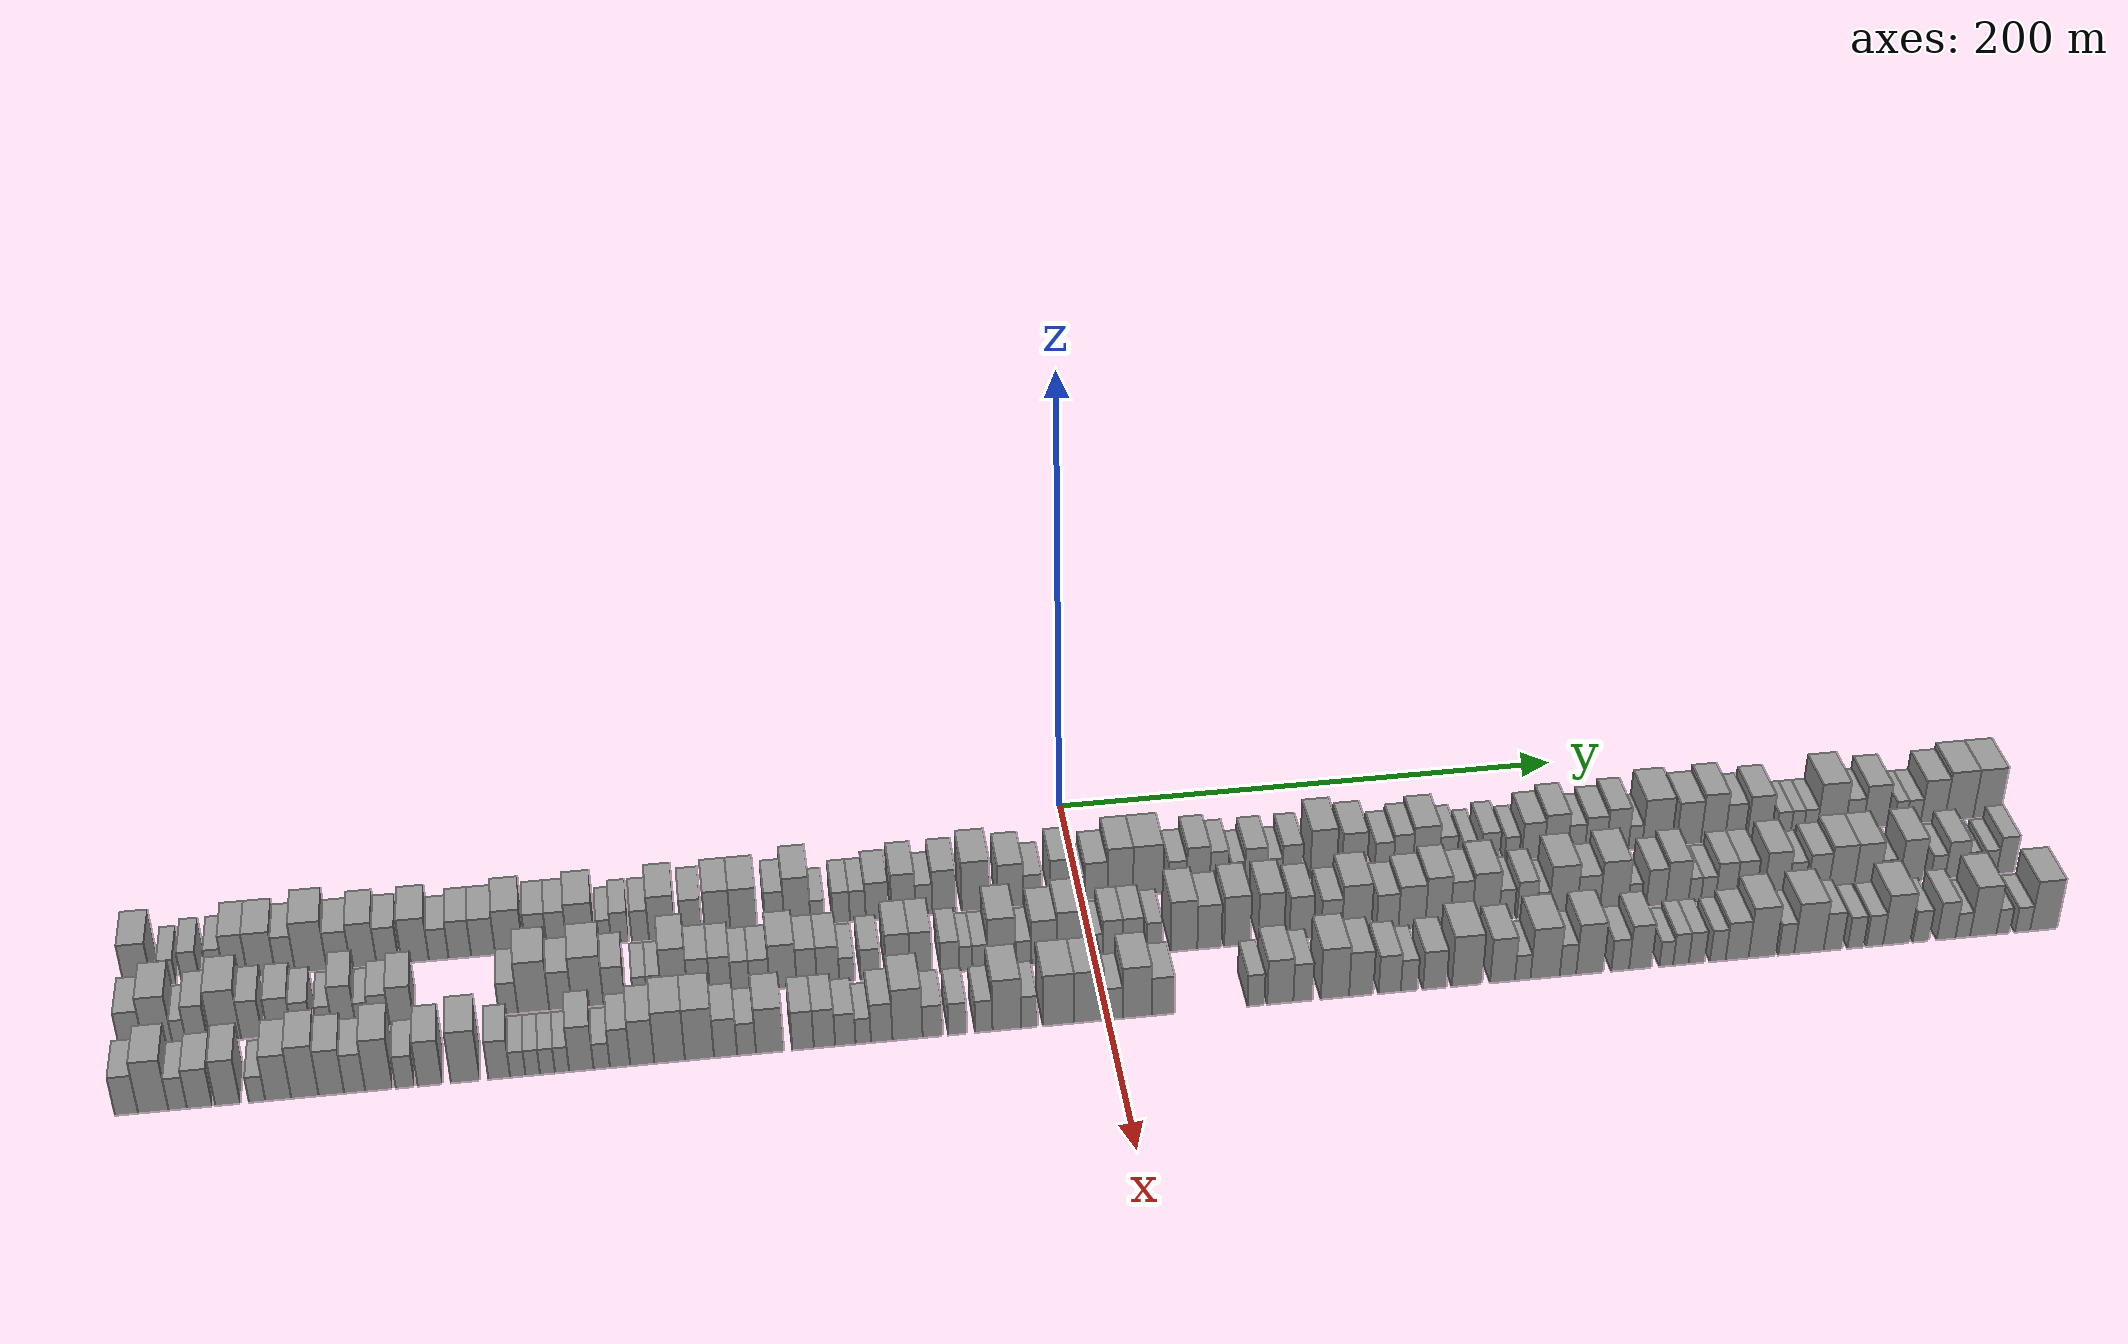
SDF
<sdf version="1.6">
 <world name="default">
  <scene>
   <sky><clouds><speed>12</speed></clouds></sky>
   <ambient>0.4 0.4 0.4 1</ambient>
   <background>0.7 0.7 0.7 1</background>
   <shadows>1</shadows>
  </scene>
  <gravity>0 0 -9.8066</gravity>
  <magnetic_field>6e-06 2.3e-05 -4.2e-05</magnetic_field>
  <physics default="0" name="default_physics" type="ode">
   <ode>
    <solver>
     <type>quick</type>
     <iters>10</iters>
     <sor>1.0</sor>
     <use_dynamic_moi_rescaling>0</use_dynamic_moi_rescaling>
    </solver>
    <constraints>
     <cfm>0</cfm>
     <erp>0.2</erp>
     <contact_max_correcting_vel>100</contact_max_correcting_vel>
     <contact_surface_layer>0.001</contact_surface_layer>
    </constraints>
   </ode>
   <max_step_size>0.004</max_step_size>
   <real_time_factor>1</real_time_factor>
   <real_time_update_rate>250</real_time_update_rate>
  </physics>
  <light name="sun" type="directional">
   <pose>0 0 10 0 0 0</pose>
   <diffuse>0.8 0.8 0.8 1</diffuse>
   <specular>0.2 0.2 0.2 1</specular>
   <attenuation>
    <range>1000</range>
    <constant>0.9</constant>
    <linear>0.01</linear>
    <quadratic>0.001</quadratic>
   </attenuation>
   <direction>-0.5 0.1 -0.9</direction>
  </light>
  <model name="building_1">
   <static>1</static>
   <pose>50.0000 -354.9391 0 0.000000 0.000000 0.000000</pose>
   <link name="link">
    <pose>0 0 10.50 0 0 0</pose>
    <collision name="collision"><geometry><box><size>20.0000 10.1219 21.0000</size></box></geometry></collision>
    <visual name="visual">
     <cast_shadows>0</cast_shadows>
     <geometry><box><size>20.0000 10.1219 21.0000</size></box></geometry>
     <material>
      <script>
       <uri>model://grey_wall/materials/scripts</uri>
       <uri>model://grey_wall/materials/textures</uri>
       <name>vrc/grey_wall</name>
      </script>
     </material>
    </visual>
   </link>
  </model>
  <model name="building_2">
   <static>1</static>
   <pose>50.0000 -343.9775 0 0.000000 0.000000 0.000000</pose>
   <link name="link">
    <pose>0 0 6.00 0 0 0</pose>
    <collision name="collision"><geometry><box><size>20.0000 5.8013 12.0000</size></box></geometry></collision>
    <visual name="visual">
     <cast_shadows>0</cast_shadows>
     <geometry><box><size>20.0000 5.8013 12.0000</size></box></geometry>
     <material>
      <script>
       <uri>model://grey_wall/materials/scripts</uri>
       <uri>model://grey_wall/materials/textures</uri>
       <name>vrc/grey_wall</name>
      </script>
     </material>
    </visual>
   </link>
  </model>
  <model name="building_3">
   <static>1</static>
   <pose>50.0000 -335.7818 0 0.000000 0.000000 0.000000</pose>
   <link name="link">
    <pose>0 0 7.50 0 0 0</pose>
    <collision name="collision"><geometry><box><size>20.0000 6.5900 15.0000</size></box></geometry></collision>
    <visual name="visual">
     <cast_shadows>0</cast_shadows>
     <geometry><box><size>20.0000 6.5900 15.0000</size></box></geometry>
     <material>
      <script>
       <uri>model://grey_wall/materials/scripts</uri>
       <uri>model://grey_wall/materials/textures</uri>
       <name>vrc/grey_wall</name>
      </script>
     </material>
    </visual>
   </link>
  </model>
  <model name="building_4">
   <static>1</static>
   <pose>50.0000 -326.4443 0 0.000000 0.000000 0.000000</pose>
   <link name="link">
    <pose>0 0 7.50 0 0 0</pose>
    <collision name="collision"><geometry><box><size>20.0000 6.0850 15.0000</size></box></geometry></collision>
    <visual name="visual">
     <cast_shadows>0</cast_shadows>
     <geometry><box><size>20.0000 6.0850 15.0000</size></box></geometry>
     <material>
      <script>
       <uri>model://grey_wall/materials/scripts</uri>
       <uri>model://grey_wall/materials/textures</uri>
       <name>vrc/grey_wall</name>
      </script>
     </material>
    </visual>
   </link>
  </model>
  <model name="building_5">
   <static>1</static>
   <pose>50.0000 -319.1303 0 0.000000 0.000000 0.000000</pose>
   <link name="link">
    <pose>0 0 10.50 0 0 0</pose>
    <collision name="collision"><geometry><box><size>20.0000 8.5431 21.0000</size></box></geometry></collision>
    <visual name="visual">
     <cast_shadows>0</cast_shadows>
     <geometry><box><size>20.0000 8.5431 21.0000</size></box></geometry>
     <material>
      <script>
       <uri>model://grey_wall/materials/scripts</uri>
       <uri>model://grey_wall/materials/textures</uri>
       <name>vrc/grey_wall</name>
      </script>
     </material>
    </visual>
   </link>
  </model>
  <model name="building_6">
   <static>1</static>
   <pose>50.0000 -309.7479 0 0.000000 0.000000 0.000000</pose>
   <link name="link">
    <pose>0 0 10.50 0 0 0</pose>
    <collision name="collision"><geometry><box><size>20.0000 10.2218 21.0000</size></box></geometry></collision>
    <visual name="visual">
     <cast_shadows>0</cast_shadows>
     <geometry><box><size>20.0000 10.2218 21.0000</size></box></geometry>
     <material>
      <script>
       <uri>model://grey_wall/materials/scripts</uri>
       <uri>model://grey_wall/materials/textures</uri>
       <name>vrc/grey_wall</name>
      </script>
     </material>
    </visual>
   </link>
  </model>
  <model name="building_7">
   <static>1</static>
   <pose>50.0000 -301.0002 0 0.000000 0.000000 0.000000</pose>
   <link name="link">
    <pose>0 0 9.00 0 0 0</pose>
    <collision name="collision"><geometry><box><size>20.0000 7.2737 18.0000</size></box></geometry></collision>
    <visual name="visual">
     <cast_shadows>0</cast_shadows>
     <geometry><box><size>20.0000 7.2737 18.0000</size></box></geometry>
     <material>
      <script>
       <uri>model://grey_wall/materials/scripts</uri>
       <uri>model://grey_wall/materials/textures</uri>
       <name>vrc/grey_wall</name>
      </script>
     </material>
    </visual>
   </link>
  </model>
  <model name="building_8">
   <static>1</static>
   <pose>50.0000 -291.5645 0 0.000000 0.000000 0.000000</pose>
   <link name="link">
    <pose>0 0 12.00 0 0 0</pose>
    <collision name="collision"><geometry><box><size>20.0000 11.5976 24.0000</size></box></geometry></collision>
    <visual name="visual">
     <cast_shadows>0</cast_shadows>
     <geometry><box><size>20.0000 11.5976 24.0000</size></box></geometry>
     <material>
      <script>
       <uri>model://grey_wall/materials/scripts</uri>
       <uri>model://grey_wall/materials/textures</uri>
       <name>vrc/grey_wall</name>
      </script>
     </material>
    </visual>
   </link>
  </model>
  <model name="building_9">
   <static>1</static>
   <pose>50.0000 -281.3838 0 0.000000 0.000000 0.000000</pose>
   <link name="link">
    <pose>0 0 9.00 0 0 0</pose>
    <collision name="collision"><geometry><box><size>20.0000 8.7638 18.0000</size></box></geometry></collision>
    <visual name="visual">
     <cast_shadows>0</cast_shadows>
     <geometry><box><size>20.0000 8.7638 18.0000</size></box></geometry>
     <material>
      <script>
       <uri>model://grey_wall/materials/scripts</uri>
       <uri>model://grey_wall/materials/textures</uri>
       <name>vrc/grey_wall</name>
      </script>
     </material>
    </visual>
   </link>
  </model>
  <model name="building_10">
   <static>1</static>
   <pose>50.0000 -272.1794 0 0.000000 0.000000 0.000000</pose>
   <link name="link">
    <pose>0 0 10.50 0 0 0</pose>
    <collision name="collision"><geometry><box><size>20.0000 9.6451 21.0000</size></box></geometry></collision>
    <visual name="visual">
     <cast_shadows>0</cast_shadows>
     <geometry><box><size>20.0000 9.6451 21.0000</size></box></geometry>
     <material>
      <script>
       <uri>model://grey_wall/materials/scripts</uri>
       <uri>model://grey_wall/materials/textures</uri>
       <name>vrc/grey_wall</name>
      </script>
     </material>
    </visual>
   </link>
  </model>
  <model name="building_11">
   <static>1</static>
   <pose>50.0000 -263.2379 0 0.000000 0.000000 0.000000</pose>
   <link name="link">
    <pose>0 0 9.00 0 0 0</pose>
    <collision name="collision"><geometry><box><size>20.0000 8.2379 18.0000</size></box></geometry></collision>
    <visual name="visual">
     <cast_shadows>0</cast_shadows>
     <geometry><box><size>20.0000 8.2379 18.0000</size></box></geometry>
     <material>
      <script>
       <uri>model://grey_wall/materials/scripts</uri>
       <uri>model://grey_wall/materials/textures</uri>
       <name>vrc/grey_wall</name>
      </script>
     </material>
    </visual>
   </link>
  </model>
  <model name="building_12">
   <static>1</static>
   <pose>50.0000 -253.0416 0 0.000000 0.000000 0.000000</pose>
   <link name="link">
    <pose>0 0 10.50 0 0 0</pose>
    <collision name="collision"><geometry><box><size>20.0000 10.1548 21.0000</size></box></geometry></collision>
    <visual name="visual">
     <cast_shadows>0</cast_shadows>
     <geometry><box><size>20.0000 10.1548 21.0000</size></box></geometry>
     <material>
      <script>
       <uri>model://grey_wall/materials/scripts</uri>
       <uri>model://grey_wall/materials/textures</uri>
       <name>vrc/grey_wall</name>
      </script>
     </material>
    </visual>
   </link>
  </model>
  <model name="building_13">
   <static>1</static>
   <pose>50.0000 -244.2923 0 0.000000 0.000000 0.000000</pose>
   <link name="link">
    <pose>0 0 7.50 0 0 0</pose>
    <collision name="collision"><geometry><box><size>20.0000 7.3437 15.0000</size></box></geometry></collision>
    <visual name="visual">
     <cast_shadows>0</cast_shadows>
     <geometry><box><size>20.0000 7.3437 15.0000</size></box></geometry>
     <material>
      <script>
       <uri>model://grey_wall/materials/scripts</uri>
       <uri>model://grey_wall/materials/textures</uri>
       <name>vrc/grey_wall</name>
      </script>
     </material>
    </visual>
   </link>
  </model>
  <model name="building_14">
   <static>1</static>
   <pose>50.0000 -236.4029 0 0.000000 0.000000 0.000000</pose>
   <link name="link">
    <pose>0 0 9.00 0 0 0</pose>
    <collision name="collision"><geometry><box><size>20.0000 8.4350 18.0000</size></box></geometry></collision>
    <visual name="visual">
     <cast_shadows>0</cast_shadows>
     <geometry><box><size>20.0000 8.4350 18.0000</size></box></geometry>
     <material>
      <script>
       <uri>model://grey_wall/materials/scripts</uri>
       <uri>model://grey_wall/materials/textures</uri>
       <name>vrc/grey_wall</name>
      </script>
     </material>
    </visual>
   </link>
  </model>
  <model name="building_15">
   <static>1</static>
   <pose>50.0000 -227.7180 0 0.000000 0.000000 0.000000</pose>
   <link name="link">
    <pose>0 0 9.00 0 0 0</pose>
    <collision name="collision"><geometry><box><size>20.0000 8.9350 18.0000</size></box></geometry></collision>
    <visual name="visual">
     <cast_shadows>0</cast_shadows>
     <geometry><box><size>20.0000 8.9350 18.0000</size></box></geometry>
     <material>
      <script>
       <uri>model://grey_wall/materials/scripts</uri>
       <uri>model://grey_wall/materials/textures</uri>
       <name>vrc/grey_wall</name>
      </script>
     </material>
    </visual>
   </link>
  </model>
  <model name="building_16">
   <static>1</static>
   <pose>50.0000 -218.0276 0 0.000000 0.000000 0.000000</pose>
   <link name="link">
    <pose>0 0 10.50 0 0 0</pose>
    <collision name="collision"><geometry><box><size>20.0000 10.4457 21.0000</size></box></geometry></collision>
    <visual name="visual">
     <cast_shadows>0</cast_shadows>
     <geometry><box><size>20.0000 10.4457 21.0000</size></box></geometry>
     <material>
      <script>
       <uri>model://grey_wall/materials/scripts</uri>
       <uri>model://grey_wall/materials/textures</uri>
       <name>vrc/grey_wall</name>
      </script>
     </material>
    </visual>
   </link>
  </model>
  <model name="building_17">
   <static>1</static>
   <pose>50.0000 -207.8202 0 0.000000 0.000000 0.000000</pose>
   <link name="link">
    <pose>0 0 9.00 0 0 0</pose>
    <collision name="collision"><geometry><box><size>20.0000 7.9692 18.0000</size></box></geometry></collision>
    <visual name="visual">
     <cast_shadows>0</cast_shadows>
     <geometry><box><size>20.0000 7.9692 18.0000</size></box></geometry>
     <material>
      <script>
       <uri>model://grey_wall/materials/scripts</uri>
       <uri>model://grey_wall/materials/textures</uri>
       <name>vrc/grey_wall</name>
      </script>
     </material>
    </visual>
   </link>
  </model>
  <model name="building_18">
   <static>1</static>
   <pose>50.0000 -200.0964 0 0.000000 0.000000 0.000000</pose>
   <link name="link">
    <pose>0 0 9.00 0 0 0</pose>
    <collision name="collision"><geometry><box><size>20.0000 7.4784 18.0000</size></box></geometry></collision>
    <visual name="visual">
     <cast_shadows>0</cast_shadows>
     <geometry><box><size>20.0000 7.4784 18.0000</size></box></geometry>
     <material>
      <script>
       <uri>model://grey_wall/materials/scripts</uri>
       <uri>model://grey_wall/materials/textures</uri>
       <name>vrc/grey_wall</name>
      </script>
     </material>
    </visual>
   </link>
  </model>
  <model name="building_19">
   <static>1</static>
   <pose>50.0000 -191.1372 0 0.000000 0.000000 0.000000</pose>
   <link name="link">
    <pose>0 0 10.50 0 0 0</pose>
    <collision name="collision"><geometry><box><size>20.0000 10.4399 21.0000</size></box></geometry></collision>
    <visual name="visual">
     <cast_shadows>0</cast_shadows>
     <geometry><box><size>20.0000 10.4399 21.0000</size></box></geometry>
     <material>
      <script>
       <uri>model://grey_wall/materials/scripts</uri>
       <uri>model://grey_wall/materials/textures</uri>
       <name>vrc/grey_wall</name>
      </script>
     </material>
    </visual>
   </link>
  </model>
  <model name="building_20">
   <static>1</static>
   <pose>50.0000 -182.3036 0 0.000000 0.000000 0.000000</pose>
   <link name="link">
    <pose>0 0 6.00 0 0 0</pose>
    <collision name="collision"><geometry><box><size>20.0000 5.2275 12.0000</size></box></geometry></collision>
    <visual name="visual">
     <cast_shadows>0</cast_shadows>
     <geometry><box><size>20.0000 5.2275 12.0000</size></box></geometry>
     <material>
      <script>
       <uri>model://grey_wall/materials/scripts</uri>
       <uri>model://grey_wall/materials/textures</uri>
       <name>vrc/grey_wall</name>
      </script>
     </material>
    </visual>
   </link>
  </model>
  <model name="building_21">
   <static>1</static>
   <pose>50.0000 -176.3457 0 0.000000 0.000000 0.000000</pose>
   <link name="link">
    <pose>0 0 7.50 0 0 0</pose>
    <collision name="collision"><geometry><box><size>20.0000 6.6882 15.0000</size></box></geometry></collision>
    <visual name="visual">
     <cast_shadows>0</cast_shadows>
     <geometry><box><size>20.0000 6.6882 15.0000</size></box></geometry>
     <material>
      <script>
       <uri>model://grey_wall/materials/scripts</uri>
       <uri>model://grey_wall/materials/textures</uri>
       <name>vrc/grey_wall</name>
      </script>
     </material>
    </visual>
   </link>
  </model>
  <model name="building_22">
   <static>1</static>
   <pose>50.0000 -168.7545 0 0.000000 0.000000 0.000000</pose>
   <link name="link">
    <pose>0 0 7.50 0 0 0</pose>
    <collision name="collision"><geometry><box><size>20.0000 6.4942 15.0000</size></box></geometry></collision>
    <visual name="visual">
     <cast_shadows>0</cast_shadows>
     <geometry><box><size>20.0000 6.4942 15.0000</size></box></geometry>
     <material>
      <script>
       <uri>model://grey_wall/materials/scripts</uri>
       <uri>model://grey_wall/materials/textures</uri>
       <name>vrc/grey_wall</name>
      </script>
     </material>
    </visual>
   </link>
  </model>
  <model name="building_23">
   <static>1</static>
   <pose>50.0000 -160.4246 0 0.000000 0.000000 0.000000</pose>
   <link name="link">
    <pose>0 0 10.50 0 0 0</pose>
    <collision name="collision"><geometry><box><size>20.0000 10.1656 21.0000</size></box></geometry></collision>
    <visual name="visual">
     <cast_shadows>0</cast_shadows>
     <geometry><box><size>20.0000 10.1656 21.0000</size></box></geometry>
     <material>
      <script>
       <uri>model://grey_wall/materials/scripts</uri>
       <uri>model://grey_wall/materials/textures</uri>
       <name>vrc/grey_wall</name>
      </script>
     </material>
    </visual>
   </link>
  </model>
  <model name="building_24">
   <static>1</static>
   <pose>50.0000 -149.3165 0 0.000000 0.000000 0.000000</pose>
   <link name="link">
    <pose>0 0 9.00 0 0 0</pose>
    <collision name="collision"><geometry><box><size>20.0000 8.0506 18.0000</size></box></geometry></collision>
    <visual name="visual">
     <cast_shadows>0</cast_shadows>
     <geometry><box><size>20.0000 8.0506 18.0000</size></box></geometry>
     <material>
      <script>
       <uri>model://grey_wall/materials/scripts</uri>
       <uri>model://grey_wall/materials/textures</uri>
       <name>vrc/grey_wall</name>
      </script>
     </material>
    </visual>
   </link>
  </model>
  <model name="building_25">
   <static>1</static>
   <pose>50.0000 -139.4782 0 0.000000 0.000000 0.000000</pose>
   <link name="link">
    <pose>0 0 10.50 0 0 0</pose>
    <collision name="collision"><geometry><box><size>20.0000 9.6259 21.0000</size></box></geometry></collision>
    <visual name="visual">
     <cast_shadows>0</cast_shadows>
     <geometry><box><size>20.0000 9.6259 21.0000</size></box></geometry>
     <material>
      <script>
       <uri>model://grey_wall/materials/scripts</uri>
       <uri>model://grey_wall/materials/textures</uri>
       <name>vrc/grey_wall</name>
      </script>
     </material>
    </visual>
   </link>
  </model>
  <model name="building_26">
   <static>1</static>
   <pose>50.0000 -129.5304 0 0.000000 0.000000 0.000000</pose>
   <link name="link">
    <pose>0 0 10.50 0 0 0</pose>
    <collision name="collision"><geometry><box><size>20.0000 10.2697 21.0000</size></box></geometry></collision>
    <visual name="visual">
     <cast_shadows>0</cast_shadows>
     <geometry><box><size>20.0000 10.2697 21.0000</size></box></geometry>
     <material>
      <script>
       <uri>model://grey_wall/materials/scripts</uri>
       <uri>model://grey_wall/materials/textures</uri>
       <name>vrc/grey_wall</name>
      </script>
     </material>
    </visual>
   </link>
  </model>
  <model name="building_27">
   <static>1</static>
   <pose>50.0000 -117.7776 0 0.000000 0.000000 0.000000</pose>
   <link name="link">
    <pose>0 0 9.00 0 0 0</pose>
    <collision name="collision"><geometry><box><size>20.0000 7.2359 18.0000</size></box></geometry></collision>
    <visual name="visual">
     <cast_shadows>0</cast_shadows>
     <geometry><box><size>20.0000 7.2359 18.0000</size></box></geometry>
     <material>
      <script>
       <uri>model://grey_wall/materials/scripts</uri>
       <uri>model://grey_wall/materials/textures</uri>
       <name>vrc/grey_wall</name>
      </script>
     </material>
    </visual>
   </link>
  </model>
  <model name="building_28">
   <static>1</static>
   <pose>50.0000 -109.1883 0 0.000000 0.000000 0.000000</pose>
   <link name="link">
    <pose>0 0 12.00 0 0 0</pose>
    <collision name="collision"><geometry><box><size>20.0000 9.9427 24.0000</size></box></geometry></collision>
    <visual name="visual">
     <cast_shadows>0</cast_shadows>
     <geometry><box><size>20.0000 9.9427 24.0000</size></box></geometry>
     <material>
      <script>
       <uri>model://grey_wall/materials/scripts</uri>
       <uri>model://grey_wall/materials/textures</uri>
       <name>vrc/grey_wall</name>
      </script>
     </material>
    </visual>
   </link>
  </model>
  <model name="building_29">
   <static>1</static>
   <pose>50.0000 -101.4819 0 0.000000 0.000000 0.000000</pose>
   <link name="link">
    <pose>0 0 6.00 0 0 0</pose>
    <collision name="collision"><geometry><box><size>20.0000 5.4701 12.0000</size></box></geometry></collision>
    <visual name="visual">
     <cast_shadows>0</cast_shadows>
     <geometry><box><size>20.0000 5.4701 12.0000</size></box></geometry>
     <material>
      <script>
       <uri>model://grey_wall/materials/scripts</uri>
       <uri>model://grey_wall/materials/textures</uri>
       <name>vrc/grey_wall</name>
      </script>
     </material>
    </visual>
   </link>
  </model>
  <model name="building_30">
   <static>1</static>
   <pose>50.0000 -92.4810 0 0.000000 0.000000 0.000000</pose>
   <link name="link">
    <pose>0 0 7.50 0 0 0</pose>
    <collision name="collision"><geometry><box><size>20.0000 6.5315 15.0000</size></box></geometry></collision>
    <visual name="visual">
     <cast_shadows>0</cast_shadows>
     <geometry><box><size>20.0000 6.5315 15.0000</size></box></geometry>
     <material>
      <script>
       <uri>model://grey_wall/materials/scripts</uri>
       <uri>model://grey_wall/materials/textures</uri>
       <name>vrc/grey_wall</name>
      </script>
     </material>
    </visual>
   </link>
  </model>
  <model name="building_31">
   <static>1</static>
   <pose>50.0000 -86.1803 0 0.000000 0.000000 0.000000</pose>
   <link name="link">
    <pose>0 0 7.50 0 0 0</pose>
    <collision name="collision"><geometry><box><size>20.0000 6.0698 15.0000</size></box></geometry></collision>
    <visual name="visual">
     <cast_shadows>0</cast_shadows>
     <geometry><box><size>20.0000 6.0698 15.0000</size></box></geometry>
     <material>
      <script>
       <uri>model://grey_wall/materials/scripts</uri>
       <uri>model://grey_wall/materials/textures</uri>
       <name>vrc/grey_wall</name>
      </script>
     </material>
    </visual>
   </link>
  </model>
  <model name="building_32">
   <static>1</static>
   <pose>50.0000 -78.6908 0 0.000000 0.000000 0.000000</pose>
   <link name="link">
    <pose>0 0 9.00 0 0 0</pose>
    <collision name="collision"><geometry><box><size>20.0000 8.9093 18.0000</size></box></geometry></collision>
    <visual name="visual">
     <cast_shadows>0</cast_shadows>
     <geometry><box><size>20.0000 8.9093 18.0000</size></box></geometry>
     <material>
      <script>
       <uri>model://grey_wall/materials/scripts</uri>
       <uri>model://grey_wall/materials/textures</uri>
       <name>vrc/grey_wall</name>
      </script>
     </material>
    </visual>
   </link>
  </model>
  <model name="building_33">
   <static>1</static>
   <pose>50.0000 -68.6561 0 0.000000 0.000000 0.000000</pose>
   <link name="link">
    <pose>0 0 10.50 0 0 0</pose>
    <collision name="collision"><geometry><box><size>20.0000 9.1600 21.0000</size></box></geometry></collision>
    <visual name="visual">
     <cast_shadows>0</cast_shadows>
     <geometry><box><size>20.0000 9.1600 21.0000</size></box></geometry>
     <material>
      <script>
       <uri>model://grey_wall/materials/scripts</uri>
       <uri>model://grey_wall/materials/textures</uri>
       <name>vrc/grey_wall</name>
      </script>
     </material>
    </visual>
   </link>
  </model>
  <model name="building_34">
   <static>1</static>
   <pose>50.0000 -60.8174 0 0.000000 0.000000 0.000000</pose>
   <link name="link">
    <pose>0 0 7.50 0 0 0</pose>
    <collision name="collision"><geometry><box><size>20.0000 6.5175 15.0000</size></box></geometry></collision>
    <visual name="visual">
     <cast_shadows>0</cast_shadows>
     <geometry><box><size>20.0000 6.5175 15.0000</size></box></geometry>
     <material>
      <script>
       <uri>model://grey_wall/materials/scripts</uri>
       <uri>model://grey_wall/materials/textures</uri>
       <name>vrc/grey_wall</name>
      </script>
     </material>
    </visual>
   </link>
  </model>
  <model name="building_35">
   <static>1</static>
   <pose>50.0000 -52.9513 0 0.000000 0.000000 0.000000</pose>
   <link name="link">
    <pose>0 0 10.50 0 0 0</pose>
    <collision name="collision"><geometry><box><size>20.0000 9.2147 21.0000</size></box></geometry></collision>
    <visual name="visual">
     <cast_shadows>0</cast_shadows>
     <geometry><box><size>20.0000 9.2147 21.0000</size></box></geometry>
     <material>
      <script>
       <uri>model://grey_wall/materials/scripts</uri>
       <uri>model://grey_wall/materials/textures</uri>
       <name>vrc/grey_wall</name>
      </script>
     </material>
    </visual>
   </link>
  </model>
  <model name="building_36">
   <static>1</static>
   <pose>50.0000 -40.8622 0 0.000000 0.000000 0.000000</pose>
   <link name="link">
    <pose>0 0 12.00 0 0 0</pose>
    <collision name="collision"><geometry><box><size>20.0000 10.9633 24.0000</size></box></geometry></collision>
    <visual name="visual">
     <cast_shadows>0</cast_shadows>
     <geometry><box><size>20.0000 10.9633 24.0000</size></box></geometry>
     <material>
      <script>
       <uri>model://grey_wall/materials/scripts</uri>
       <uri>model://grey_wall/materials/textures</uri>
       <name>vrc/grey_wall</name>
      </script>
     </material>
    </visual>
   </link>
  </model>
  <model name="building_37">
   <static>1</static>
   <pose>50.0000 -27.4583 0 0.000000 0.000000 0.000000</pose>
   <link name="link">
    <pose>0 0 10.50 0 0 0</pose>
    <collision name="collision"><geometry><box><size>20.0000 9.8445 21.0000</size></box></geometry></collision>
    <visual name="visual">
     <cast_shadows>0</cast_shadows>
     <geometry><box><size>20.0000 9.8445 21.0000</size></box></geometry>
     <material>
      <script>
       <uri>model://grey_wall/materials/scripts</uri>
       <uri>model://grey_wall/materials/textures</uri>
       <name>vrc/grey_wall</name>
      </script>
     </material>
    </visual>
   </link>
  </model>
  <model name="building_38">
   <static>1</static>
   <pose>50.0000 -18.8467 0 0.000000 0.000000 0.000000</pose>
   <link name="link">
    <pose>0 0 7.50 0 0 0</pose>
    <collision name="collision"><geometry><box><size>20.0000 7.3786 15.0000</size></box></geometry></collision>
    <visual name="visual">
     <cast_shadows>0</cast_shadows>
     <geometry><box><size>20.0000 7.3786 15.0000</size></box></geometry>
     <material>
      <script>
       <uri>model://grey_wall/materials/scripts</uri>
       <uri>model://grey_wall/materials/textures</uri>
       <name>vrc/grey_wall</name>
      </script>
     </material>
    </visual>
   </link>
  </model>
  <model name="building_39">
   <static>1</static>
   <pose>50.0000 -7.9230 0 0.000000 0.000000 0.000000</pose>
   <link name="link">
    <pose>0 0 10.50 0 0 0</pose>
    <collision name="collision"><geometry><box><size>20.0000 8.4687 21.0000</size></box></geometry></collision>
    <visual name="visual">
     <cast_shadows>0</cast_shadows>
     <geometry><box><size>20.0000 8.4687 21.0000</size></box></geometry>
     <material>
      <script>
       <uri>model://grey_wall/materials/scripts</uri>
       <uri>model://grey_wall/materials/textures</uri>
       <name>vrc/grey_wall</name>
      </script>
     </material>
    </visual>
   </link>
  </model>
  <model name="building_40">
   <static>1</static>
   <pose>50.0000 -1.2210 0 0.000000 0.000000 0.000000</pose>
   <link name="link">
    <pose>0 0 6.00 0 0 0</pose>
    <collision name="collision"><geometry><box><size>20.0000 4.9352 12.0000</size></box></geometry></collision>
    <visual name="visual">
     <cast_shadows>0</cast_shadows>
     <geometry><box><size>20.0000 4.9352 12.0000</size></box></geometry>
     <material>
      <script>
       <uri>model://grey_wall/materials/scripts</uri>
       <uri>model://grey_wall/materials/textures</uri>
       <name>vrc/grey_wall</name>
      </script>
     </material>
    </visual>
   </link>
  </model>
  <model name="building_41">
   <static>1</static>
   <pose>50.0000 5.6568 0 0.000000 0.000000 0.000000</pose>
   <link name="link">
    <pose>0 0 9.00 0 0 0</pose>
    <collision name="collision"><geometry><box><size>20.0000 8.8205 18.0000</size></box></geometry></collision>
    <visual name="visual">
     <cast_shadows>0</cast_shadows>
     <geometry><box><size>20.0000 8.8205 18.0000</size></box></geometry>
     <material>
      <script>
       <uri>model://grey_wall/materials/scripts</uri>
       <uri>model://grey_wall/materials/textures</uri>
       <name>vrc/grey_wall</name>
      </script>
     </material>
    </visual>
   </link>
  </model>
  <model name="building_42">
   <static>1</static>
   <pose>50.0000 15.0740 0 0.000000 0.000000 0.000000</pose>
   <link name="link">
    <pose>0 0 12.00 0 0 0</pose>
    <collision name="collision"><geometry><box><size>20.0000 10.0138 24.0000</size></box></geometry></collision>
    <visual name="visual">
     <cast_shadows>0</cast_shadows>
     <geometry><box><size>20.0000 10.0138 24.0000</size></box></geometry>
     <material>
      <script>
       <uri>model://grey_wall/materials/scripts</uri>
       <uri>model://grey_wall/materials/textures</uri>
       <name>vrc/grey_wall</name>
      </script>
     </material>
    </visual>
   </link>
  </model>
  <model name="building_43">
   <static>1</static>
   <pose>50.0000 25.9622 0 0.000000 0.000000 0.000000</pose>
   <link name="link">
    <pose>0 0 12.00 0 0 0</pose>
    <collision name="collision"><geometry><box><size>20.0000 11.7626 24.0000</size></box></geometry></collision>
    <visual name="visual">
     <cast_shadows>0</cast_shadows>
     <geometry><box><size>20.0000 11.7626 24.0000</size></box></geometry>
     <material>
      <script>
       <uri>model://grey_wall/materials/scripts</uri>
       <uri>model://grey_wall/materials/textures</uri>
       <name>vrc/grey_wall</name>
      </script>
     </material>
    </visual>
   </link>
  </model>
  <model name="building_44">
   <static>1</static>
   <pose>50.0000 37.4230 0 0.000000 0.000000 0.000000</pose>
   <link name="link">
    <pose>0 0 7.50 0 0 0</pose>
    <collision name="collision"><geometry><box><size>20.0000 7.1590 15.0000</size></box></geometry></collision>
    <visual name="visual">
     <cast_shadows>0</cast_shadows>
     <geometry><box><size>20.0000 7.1590 15.0000</size></box></geometry>
     <material>
      <script>
       <uri>model://grey_wall/materials/scripts</uri>
       <uri>model://grey_wall/materials/textures</uri>
       <name>vrc/grey_wall</name>
      </script>
     </material>
    </visual>
   </link>
  </model>
  <model name="building_45">
   <static>1</static>
   <pose>50.0000 45.5226 0 0.000000 0.000000 0.000000</pose>
   <link name="link">
    <pose>0 0 10.50 0 0 0</pose>
    <collision name="collision"><geometry><box><size>20.0000 9.0401 21.0000</size></box></geometry></collision>
    <visual name="visual">
     <cast_shadows>0</cast_shadows>
     <geometry><box><size>20.0000 9.0401 21.0000</size></box></geometry>
     <material>
      <script>
       <uri>model://grey_wall/materials/scripts</uri>
       <uri>model://grey_wall/materials/textures</uri>
       <name>vrc/grey_wall</name>
      </script>
     </material>
    </visual>
   </link>
  </model>
  <model name="building_46">
   <static>1</static>
   <pose>50.0000 53.6697 0 0.000000 0.000000 0.000000</pose>
   <link name="link">
    <pose>0 0 9.00 0 0 0</pose>
    <collision name="collision"><geometry><box><size>20.0000 7.2541 18.0000</size></box></geometry></collision>
    <visual name="visual">
     <cast_shadows>0</cast_shadows>
     <geometry><box><size>20.0000 7.2541 18.0000</size></box></geometry>
     <material>
      <script>
       <uri>model://grey_wall/materials/scripts</uri>
       <uri>model://grey_wall/materials/textures</uri>
       <name>vrc/grey_wall</name>
      </script>
     </material>
    </visual>
   </link>
  </model>
  <model name="building_47">
   <static>1</static>
   <pose>50.0000 60.9880 0 0.000000 0.000000 0.000000</pose>
   <link name="link">
    <pose>0 0 6.00 0 0 0</pose>
    <collision name="collision"><geometry><box><size>20.0000 5.3825 12.0000</size></box></geometry></collision>
    <visual name="visual">
     <cast_shadows>0</cast_shadows>
     <geometry><box><size>20.0000 5.3825 12.0000</size></box></geometry>
     <material>
      <script>
       <uri>model://grey_wall/materials/scripts</uri>
       <uri>model://grey_wall/materials/textures</uri>
       <name>vrc/grey_wall</name>
      </script>
     </material>
    </visual>
   </link>
  </model>
  <model name="building_48">
   <static>1</static>
   <pose>50.0000 68.0890 0 0.000000 0.000000 0.000000</pose>
   <link name="link">
    <pose>0 0 9.00 0 0 0</pose>
    <collision name="collision"><geometry><box><size>20.0000 8.8196 18.0000</size></box></geometry></collision>
    <visual name="visual">
     <cast_shadows>0</cast_shadows>
     <geometry><box><size>20.0000 8.8196 18.0000</size></box></geometry>
     <material>
      <script>
       <uri>model://grey_wall/materials/scripts</uri>
       <uri>model://grey_wall/materials/textures</uri>
       <name>vrc/grey_wall</name>
      </script>
     </material>
    </visual>
   </link>
  </model>
  <model name="building_49">
   <static>1</static>
   <pose>50.0000 75.4535 0 0.000000 0.000000 0.000000</pose>
   <link name="link">
    <pose>0 0 6.00 0 0 0</pose>
    <collision name="collision"><geometry><box><size>20.0000 5.9093 12.0000</size></box></geometry></collision>
    <visual name="visual">
     <cast_shadows>0</cast_shadows>
     <geometry><box><size>20.0000 5.9093 12.0000</size></box></geometry>
     <material>
      <script>
       <uri>model://grey_wall/materials/scripts</uri>
       <uri>model://grey_wall/materials/textures</uri>
       <name>vrc/grey_wall</name>
      </script>
     </material>
    </visual>
   </link>
  </model>
  <model name="building_50">
   <static>1</static>
   <pose>50.0000 82.3979 0 0.000000 0.000000 0.000000</pose>
   <link name="link">
    <pose>0 0 9.00 0 0 0</pose>
    <collision name="collision"><geometry><box><size>20.0000 7.9795 18.0000</size></box></geometry></collision>
    <visual name="visual">
     <cast_shadows>0</cast_shadows>
     <geometry><box><size>20.0000 7.9795 18.0000</size></box></geometry>
     <material>
      <script>
       <uri>model://grey_wall/materials/scripts</uri>
       <uri>model://grey_wall/materials/textures</uri>
       <name>vrc/grey_wall</name>
      </script>
     </material>
    </visual>
   </link>
  </model>
  <model name="building_51">
   <static>1</static>
   <pose>50.0000 94.6250 0 0.000000 0.000000 0.000000</pose>
   <link name="link">
    <pose>0 0 12.00 0 0 0</pose>
    <collision name="collision"><geometry><box><size>20.0000 10.4747 24.0000</size></box></geometry></collision>
    <visual name="visual">
     <cast_shadows>0</cast_shadows>
     <geometry><box><size>20.0000 10.4747 24.0000</size></box></geometry>
     <material>
      <script>
       <uri>model://grey_wall/materials/scripts</uri>
       <uri>model://grey_wall/materials/textures</uri>
       <name>vrc/grey_wall</name>
      </script>
     </material>
    </visual>
   </link>
  </model>
  <model name="building_52">
   <static>1</static>
   <pose>50.0000 106.8506 0 0.000000 0.000000 0.000000</pose>
   <link name="link">
    <pose>0 0 10.50 0 0 0</pose>
    <collision name="collision"><geometry><box><size>20.0000 9.9764 21.0000</size></box></geometry></collision>
    <visual name="visual">
     <cast_shadows>0</cast_shadows>
     <geometry><box><size>20.0000 9.9764 21.0000</size></box></geometry>
     <material>
      <script>
       <uri>model://grey_wall/materials/scripts</uri>
       <uri>model://grey_wall/materials/textures</uri>
       <name>vrc/grey_wall</name>
      </script>
     </material>
    </visual>
   </link>
  </model>
  <model name="building_53">
   <static>1</static>
   <pose>50.0000 118.5777 0 0.000000 0.000000 0.000000</pose>
   <link name="link">
    <pose>0 0 7.50 0 0 0</pose>
    <collision name="collision"><geometry><box><size>20.0000 7.4779 15.0000</size></box></geometry></collision>
    <visual name="visual">
     <cast_shadows>0</cast_shadows>
     <geometry><box><size>20.0000 7.4779 15.0000</size></box></geometry>
     <material>
      <script>
       <uri>model://grey_wall/materials/scripts</uri>
       <uri>model://grey_wall/materials/textures</uri>
       <name>vrc/grey_wall</name>
      </script>
     </material>
    </visual>
   </link>
  </model>
  <model name="building_54">
   <static>1</static>
   <pose>50.0000 126.1805 0 0.000000 0.000000 0.000000</pose>
   <link name="link">
    <pose>0 0 9.00 0 0 0</pose>
    <collision name="collision"><geometry><box><size>20.0000 7.7276 18.0000</size></box></geometry></collision>
    <visual name="visual">
     <cast_shadows>0</cast_shadows>
     <geometry><box><size>20.0000 7.7276 18.0000</size></box></geometry>
     <material>
      <script>
       <uri>model://grey_wall/materials/scripts</uri>
       <uri>model://grey_wall/materials/textures</uri>
       <name>vrc/grey_wall</name>
      </script>
     </material>
    </visual>
   </link>
  </model>
  <model name="building_55">
   <static>1</static>
   <pose>50.0000 135.2170 0 0.000000 0.000000 0.000000</pose>
   <link name="link">
    <pose>0 0 10.50 0 0 0</pose>
    <collision name="collision"><geometry><box><size>20.0000 10.3455 21.0000</size></box></geometry></collision>
    <visual name="visual">
     <cast_shadows>0</cast_shadows>
     <geometry><box><size>20.0000 10.3455 21.0000</size></box></geometry>
     <material>
      <script>
       <uri>model://grey_wall/materials/scripts</uri>
       <uri>model://grey_wall/materials/textures</uri>
       <name>vrc/grey_wall</name>
      </script>
     </material>
    </visual>
   </link>
  </model>
  <model name="building_56">
   <static>1</static>
   <pose>50.0000 143.9583 0 0.000000 0.000000 0.000000</pose>
   <link name="link">
    <pose>0 0 7.50 0 0 0</pose>
    <collision name="collision"><geometry><box><size>20.0000 7.1372 15.0000</size></box></geometry></collision>
    <visual name="visual">
     <cast_shadows>0</cast_shadows>
     <geometry><box><size>20.0000 7.1372 15.0000</size></box></geometry>
     <material>
      <script>
       <uri>model://grey_wall/materials/scripts</uri>
       <uri>model://grey_wall/materials/textures</uri>
       <name>vrc/grey_wall</name>
      </script>
     </material>
    </visual>
   </link>
  </model>
  <model name="building_57">
   <static>1</static>
   <pose>50.0000 152.3518 0 0.000000 0.000000 0.000000</pose>
   <link name="link">
    <pose>0 0 6.00 0 0 0</pose>
    <collision name="collision"><geometry><box><size>20.0000 5.6498 12.0000</size></box></geometry></collision>
    <visual name="visual">
     <cast_shadows>0</cast_shadows>
     <geometry><box><size>20.0000 5.6498 12.0000</size></box></geometry>
     <material>
      <script>
       <uri>model://grey_wall/materials/scripts</uri>
       <uri>model://grey_wall/materials/textures</uri>
       <name>vrc/grey_wall</name>
      </script>
     </material>
    </visual>
   </link>
  </model>
  <model name="building_58">
   <static>1</static>
   <pose>50.0000 160.8615 0 0.000000 0.000000 0.000000</pose>
   <link name="link">
    <pose>0 0 7.50 0 0 0</pose>
    <collision name="collision"><geometry><box><size>20.0000 7.3695 15.0000</size></box></geometry></collision>
    <visual name="visual">
     <cast_shadows>0</cast_shadows>
     <geometry><box><size>20.0000 7.3695 15.0000</size></box></geometry>
     <material>
      <script>
       <uri>model://grey_wall/materials/scripts</uri>
       <uri>model://grey_wall/materials/textures</uri>
       <name>vrc/grey_wall</name>
      </script>
     </material>
    </visual>
   </link>
  </model>
  <model name="building_59">
   <static>1</static>
   <pose>50.0000 169.4913 0 0.000000 0.000000 0.000000</pose>
   <link name="link">
    <pose>0 0 6.00 0 0 0</pose>
    <collision name="collision"><geometry><box><size>20.0000 5.8902 12.0000</size></box></geometry></collision>
    <visual name="visual">
     <cast_shadows>0</cast_shadows>
     <geometry><box><size>20.0000 5.8902 12.0000</size></box></geometry>
     <material>
      <script>
       <uri>model://grey_wall/materials/scripts</uri>
       <uri>model://grey_wall/materials/textures</uri>
       <name>vrc/grey_wall</name>
      </script>
     </material>
    </visual>
   </link>
  </model>
  <model name="building_60">
   <static>1</static>
   <pose>50.0000 177.8740 0 0.000000 0.000000 0.000000</pose>
   <link name="link">
    <pose>0 0 9.00 0 0 0</pose>
    <collision name="collision"><geometry><box><size>20.0000 8.8753 18.0000</size></box></geometry></collision>
    <visual name="visual">
     <cast_shadows>0</cast_shadows>
     <geometry><box><size>20.0000 8.8753 18.0000</size></box></geometry>
     <material>
      <script>
       <uri>model://grey_wall/materials/scripts</uri>
       <uri>model://grey_wall/materials/textures</uri>
       <name>vrc/grey_wall</name>
      </script>
     </material>
    </visual>
   </link>
  </model>
  <model name="building_61">
   <static>1</static>
   <pose>50.0000 187.0451 0 0.000000 0.000000 0.000000</pose>
   <link name="link">
    <pose>0 0 10.50 0 0 0</pose>
    <collision name="collision"><geometry><box><size>20.0000 9.4669 21.0000</size></box></geometry></collision>
    <visual name="visual">
     <cast_shadows>0</cast_shadows>
     <geometry><box><size>20.0000 9.4669 21.0000</size></box></geometry>
     <material>
      <script>
       <uri>model://grey_wall/materials/scripts</uri>
       <uri>model://grey_wall/materials/textures</uri>
       <name>vrc/grey_wall</name>
      </script>
     </material>
    </visual>
   </link>
  </model>
  <model name="building_62">
   <static>1</static>
   <pose>50.0000 195.2270 0 0.000000 0.000000 0.000000</pose>
   <link name="link">
    <pose>0 0 7.50 0 0 0</pose>
    <collision name="collision"><geometry><box><size>20.0000 6.8969 15.0000</size></box></geometry></collision>
    <visual name="visual">
     <cast_shadows>0</cast_shadows>
     <geometry><box><size>20.0000 6.8969 15.0000</size></box></geometry>
     <material>
      <script>
       <uri>model://grey_wall/materials/scripts</uri>
       <uri>model://grey_wall/materials/textures</uri>
       <name>vrc/grey_wall</name>
      </script>
     </material>
    </visual>
   </link>
  </model>
  <model name="building_63">
   <static>1</static>
   <pose>50.0000 203.0137 0 0.000000 0.000000 0.000000</pose>
   <link name="link">
    <pose>0 0 9.00 0 0 0</pose>
    <collision name="collision"><geometry><box><size>20.0000 8.6763 18.0000</size></box></geometry></collision>
    <visual name="visual">
     <cast_shadows>0</cast_shadows>
     <geometry><box><size>20.0000 8.6763 18.0000</size></box></geometry>
     <material>
      <script>
       <uri>model://grey_wall/materials/scripts</uri>
       <uri>model://grey_wall/materials/textures</uri>
       <name>vrc/grey_wall</name>
      </script>
     </material>
    </visual>
   </link>
  </model>
  <model name="building_64">
   <static>1</static>
   <pose>50.0000 211.7805 0 0.000000 0.000000 0.000000</pose>
   <link name="link">
    <pose>0 0 10.50 0 0 0</pose>
    <collision name="collision"><geometry><box><size>20.0000 8.8573 21.0000</size></box></geometry></collision>
    <visual name="visual">
     <cast_shadows>0</cast_shadows>
     <geometry><box><size>20.0000 8.8573 21.0000</size></box></geometry>
     <material>
      <script>
       <uri>model://grey_wall/materials/scripts</uri>
       <uri>model://grey_wall/materials/textures</uri>
       <name>vrc/grey_wall</name>
      </script>
     </material>
    </visual>
   </link>
  </model>
  <model name="building_65">
   <static>1</static>
   <pose>50.0000 218.9763 0 0.000000 0.000000 0.000000</pose>
   <link name="link">
    <pose>0 0 6.00 0 0 0</pose>
    <collision name="collision"><geometry><box><size>20.0000 5.5345 12.0000</size></box></geometry></collision>
    <visual name="visual">
     <cast_shadows>0</cast_shadows>
     <geometry><box><size>20.0000 5.5345 12.0000</size></box></geometry>
     <material>
      <script>
       <uri>model://grey_wall/materials/scripts</uri>
       <uri>model://grey_wall/materials/textures</uri>
       <name>vrc/grey_wall</name>
      </script>
     </material>
    </visual>
   </link>
  </model>
  <model name="building_66">
   <static>1</static>
   <pose>50.0000 227.6906 0 0.000000 0.000000 0.000000</pose>
   <link name="link">
    <pose>0 0 12.00 0 0 0</pose>
    <collision name="collision"><geometry><box><size>20.0000 11.8941 24.0000</size></box></geometry></collision>
    <visual name="visual">
     <cast_shadows>0</cast_shadows>
     <geometry><box><size>20.0000 11.8941 24.0000</size></box></geometry>
     <material>
      <script>
       <uri>model://grey_wall/materials/scripts</uri>
       <uri>model://grey_wall/materials/textures</uri>
       <name>vrc/grey_wall</name>
      </script>
     </material>
    </visual>
   </link>
  </model>
  <model name="building_67">
   <static>1</static>
   <pose>50.0000 240.5784 0 0.000000 0.000000 0.000000</pose>
   <link name="link">
    <pose>0 0 10.50 0 0 0</pose>
    <collision name="collision"><geometry><box><size>20.0000 9.8814 21.0000</size></box></geometry></collision>
    <visual name="visual">
     <cast_shadows>0</cast_shadows>
     <geometry><box><size>20.0000 9.8814 21.0000</size></box></geometry>
     <material>
      <script>
       <uri>model://grey_wall/materials/scripts</uri>
       <uri>model://grey_wall/materials/textures</uri>
       <name>vrc/grey_wall</name>
      </script>
     </material>
    </visual>
   </link>
  </model>
  <model name="building_68">
   <static>1</static>
   <pose>50.0000 250.3855 0 0.000000 0.000000 0.000000</pose>
   <link name="link">
    <pose>0 0 12.00 0 0 0</pose>
    <collision name="collision"><geometry><box><size>20.0000 9.7328 24.0000</size></box></geometry></collision>
    <visual name="visual">
     <cast_shadows>0</cast_shadows>
     <geometry><box><size>20.0000 9.7328 24.0000</size></box></geometry>
     <material>
      <script>
       <uri>model://grey_wall/materials/scripts</uri>
       <uri>model://grey_wall/materials/textures</uri>
       <name>vrc/grey_wall</name>
      </script>
     </material>
    </visual>
   </link>
  </model>
  <model name="building_69">
   <static>1</static>
   <pose>50.0000 259.2750 0 0.000000 0.000000 0.000000</pose>
   <link name="link">
    <pose>0 0 9.00 0 0 0</pose>
    <collision name="collision"><geometry><box><size>20.0000 8.0463 18.0000</size></box></geometry></collision>
    <visual name="visual">
     <cast_shadows>0</cast_shadows>
     <geometry><box><size>20.0000 8.0463 18.0000</size></box></geometry>
     <material>
      <script>
       <uri>model://grey_wall/materials/scripts</uri>
       <uri>model://grey_wall/materials/textures</uri>
       <name>vrc/grey_wall</name>
      </script>
     </material>
    </visual>
   </link>
  </model>
  <model name="building_70">
   <static>1</static>
   <pose>50.0000 269.1923 0 0.000000 0.000000 0.000000</pose>
   <link name="link">
    <pose>0 0 10.50 0 0 0</pose>
    <collision name="collision"><geometry><box><size>20.0000 9.7882 21.0000</size></box></geometry></collision>
    <visual name="visual">
     <cast_shadows>0</cast_shadows>
     <geometry><box><size>20.0000 9.7882 21.0000</size></box></geometry>
     <material>
      <script>
       <uri>model://grey_wall/materials/scripts</uri>
       <uri>model://grey_wall/materials/textures</uri>
       <name>vrc/grey_wall</name>
      </script>
     </material>
    </visual>
   </link>
  </model>
  <model name="building_71">
   <static>1</static>
   <pose>50.0000 279.0514 0 0.000000 0.000000 0.000000</pose>
   <link name="link">
    <pose>0 0 6.00 0 0 0</pose>
    <collision name="collision"><geometry><box><size>20.0000 5.9301 12.0000</size></box></geometry></collision>
    <visual name="visual">
     <cast_shadows>0</cast_shadows>
     <geometry><box><size>20.0000 5.9301 12.0000</size></box></geometry>
     <material>
      <script>
       <uri>model://grey_wall/materials/scripts</uri>
       <uri>model://grey_wall/materials/textures</uri>
       <name>vrc/grey_wall</name>
      </script>
     </material>
    </visual>
   </link>
  </model>
  <model name="building_72">
   <static>1</static>
   <pose>50.0000 284.6004 0 0.000000 0.000000 0.000000</pose>
   <link name="link">
    <pose>0 0 6.00 0 0 0</pose>
    <collision name="collision"><geometry><box><size>20.0000 5.1681 12.0000</size></box></geometry></collision>
    <visual name="visual">
     <cast_shadows>0</cast_shadows>
     <geometry><box><size>20.0000 5.1681 12.0000</size></box></geometry>
     <material>
      <script>
       <uri>model://grey_wall/materials/scripts</uri>
       <uri>model://grey_wall/materials/textures</uri>
       <name>vrc/grey_wall</name>
      </script>
     </material>
    </visual>
   </link>
  </model>
  <model name="building_73">
   <static>1</static>
   <pose>50.0000 289.9048 0 0.000000 0.000000 0.000000</pose>
   <link name="link">
    <pose>0 0 6.00 0 0 0</pose>
    <collision name="collision"><geometry><box><size>20.0000 5.4407 12.0000</size></box></geometry></collision>
    <visual name="visual">
     <cast_shadows>0</cast_shadows>
     <geometry><box><size>20.0000 5.4407 12.0000</size></box></geometry>
     <material>
      <script>
       <uri>model://grey_wall/materials/scripts</uri>
       <uri>model://grey_wall/materials/textures</uri>
       <name>vrc/grey_wall</name>
      </script>
     </material>
    </visual>
   </link>
  </model>
  <model name="building_74">
   <static>1</static>
   <pose>50.0000 298.3838 0 0.000000 0.000000 0.000000</pose>
   <link name="link">
    <pose>0 0 12.00 0 0 0</pose>
    <collision name="collision"><geometry><box><size>20.0000 11.5172 24.0000</size></box></geometry></collision>
    <visual name="visual">
     <cast_shadows>0</cast_shadows>
     <geometry><box><size>20.0000 11.5172 24.0000</size></box></geometry>
     <material>
      <script>
       <uri>model://grey_wall/materials/scripts</uri>
       <uri>model://grey_wall/materials/textures</uri>
       <name>vrc/grey_wall</name>
      </script>
     </material>
    </visual>
   </link>
  </model>
  <model name="building_75">
   <static>1</static>
   <pose>50.0000 307.8314 0 0.000000 0.000000 0.000000</pose>
   <link name="link">
    <pose>0 0 7.50 0 0 0</pose>
    <collision name="collision"><geometry><box><size>20.0000 7.3780 15.0000</size></box></geometry></collision>
    <visual name="visual">
     <cast_shadows>0</cast_shadows>
     <geometry><box><size>20.0000 7.3780 15.0000</size></box></geometry>
     <material>
      <script>
       <uri>model://grey_wall/materials/scripts</uri>
       <uri>model://grey_wall/materials/textures</uri>
       <name>vrc/grey_wall</name>
      </script>
     </material>
    </visual>
   </link>
  </model>
  <model name="building_76">
   <static>1</static>
   <pose>50.0000 316.4423 0 0.000000 0.000000 0.000000</pose>
   <link name="link">
    <pose>0 0 10.50 0 0 0</pose>
    <collision name="collision"><geometry><box><size>20.0000 9.8438 21.0000</size></box></geometry></collision>
    <visual name="visual">
     <cast_shadows>0</cast_shadows>
     <geometry><box><size>20.0000 9.8438 21.0000</size></box></geometry>
     <material>
      <script>
       <uri>model://grey_wall/materials/scripts</uri>
       <uri>model://grey_wall/materials/textures</uri>
       <name>vrc/grey_wall</name>
      </script>
     </material>
    </visual>
   </link>
  </model>
  <model name="building_77">
   <static>1</static>
   <pose>50.0000 326.8547 0 0.000000 0.000000 0.000000</pose>
   <link name="link">
    <pose>0 0 6.00 0 0 0</pose>
    <collision name="collision"><geometry><box><size>20.0000 4.9808 12.0000</size></box></geometry></collision>
    <visual name="visual">
     <cast_shadows>0</cast_shadows>
     <geometry><box><size>20.0000 4.9808 12.0000</size></box></geometry>
     <material>
      <script>
       <uri>model://grey_wall/materials/scripts</uri>
       <uri>model://grey_wall/materials/textures</uri>
       <name>vrc/grey_wall</name>
      </script>
     </material>
    </visual>
   </link>
  </model>
  <model name="building_78">
   <static>1</static>
   <pose>50.0000 332.3177 0 0.000000 0.000000 0.000000</pose>
   <link name="link">
    <pose>0 0 6.00 0 0 0</pose>
    <collision name="collision"><geometry><box><size>20.0000 5.9453 12.0000</size></box></geometry></collision>
    <visual name="visual">
     <cast_shadows>0</cast_shadows>
     <geometry><box><size>20.0000 5.9453 12.0000</size></box></geometry>
     <material>
      <script>
       <uri>model://grey_wall/materials/scripts</uri>
       <uri>model://grey_wall/materials/textures</uri>
       <name>vrc/grey_wall</name>
      </script>
     </material>
    </visual>
   </link>
  </model>
  <model name="building_79">
   <static>1</static>
   <pose>50.0000 340.2331 0 0.000000 0.000000 0.000000</pose>
   <link name="link">
    <pose>0 0 10.50 0 0 0</pose>
    <collision name="collision"><geometry><box><size>20.0000 9.8855 21.0000</size></box></geometry></collision>
    <visual name="visual">
     <cast_shadows>0</cast_shadows>
     <geometry><box><size>20.0000 9.8855 21.0000</size></box></geometry>
     <material>
      <script>
       <uri>model://grey_wall/materials/scripts</uri>
       <uri>model://grey_wall/materials/textures</uri>
       <name>vrc/grey_wall</name>
      </script>
     </material>
    </visual>
   </link>
  </model>
  <model name="building_80">
   <static>1</static>
   <pose>50.0000 351.0403 0 0.000000 0.000000 0.000000</pose>
   <link name="link">
    <pose>0 0 12.00 0 0 0</pose>
    <collision name="collision"><geometry><box><size>20.0000 11.7289 24.0000</size></box></geometry></collision>
    <visual name="visual">
     <cast_shadows>0</cast_shadows>
     <geometry><box><size>20.0000 11.7289 24.0000</size></box></geometry>
     <material>
      <script>
       <uri>model://grey_wall/materials/scripts</uri>
       <uri>model://grey_wall/materials/textures</uri>
       <name>vrc/grey_wall</name>
      </script>
     </material>
    </visual>
   </link>
  </model>
  <model name="building_81">
   <static>1</static>
   <pose>50.0000 362.5758 0 0.000000 0.000000 0.000000</pose>
   <link name="link">
    <pose>0 0 12.00 0 0 0</pose>
    <collision name="collision"><geometry><box><size>20.0000 11.3421 24.0000</size></box></geometry></collision>
    <visual name="visual">
     <cast_shadows>0</cast_shadows>
     <geometry><box><size>20.0000 11.3421 24.0000</size></box></geometry>
     <material>
      <script>
       <uri>model://grey_wall/materials/scripts</uri>
       <uri>model://grey_wall/materials/textures</uri>
       <name>vrc/grey_wall</name>
      </script>
     </material>
    </visual>
   </link>
  </model>
  <model name="building_82">
   <static>1</static>
   <pose>85.0000 -354.7007 0 0.000000 0.000000 0.000000</pose>
   <link name="link">
    <pose>0 0 9.00 0 0 0</pose>
    <collision name="collision"><geometry><box><size>20.0000 8.5985 18.0000</size></box></geometry></collision>
    <visual name="visual">
     <cast_shadows>0</cast_shadows>
     <geometry><box><size>20.0000 8.5985 18.0000</size></box></geometry>
     <material>
      <script>
       <uri>model://grey_wall/materials/scripts</uri>
       <uri>model://grey_wall/materials/textures</uri>
       <name>vrc/grey_wall</name>
      </script>
     </material>
    </visual>
   </link>
  </model>
  <model name="building_83">
   <static>1</static>
   <pose>85.0000 -345.2145 0 0.000000 0.000000 0.000000</pose>
   <link name="link">
    <pose>0 0 12.00 0 0 0</pose>
    <collision name="collision"><geometry><box><size>20.0000 10.3740 24.0000</size></box></geometry></collision>
    <visual name="visual">
     <cast_shadows>0</cast_shadows>
     <geometry><box><size>20.0000 10.3740 24.0000</size></box></geometry>
     <material>
      <script>
       <uri>model://grey_wall/materials/scripts</uri>
       <uri>model://grey_wall/materials/textures</uri>
       <name>vrc/grey_wall</name>
      </script>
     </material>
    </visual>
   </link>
  </model>
  <model name="building_84">
   <static>1</static>
   <pose>85.0000 -337.5920 0 0.000000 0.000000 0.000000</pose>
   <link name="link">
    <pose>0 0 6.00 0 0 0</pose>
    <collision name="collision"><geometry><box><size>20.0000 4.8711 12.0000</size></box></geometry></collision>
    <visual name="visual">
     <cast_shadows>0</cast_shadows>
     <geometry><box><size>20.0000 4.8711 12.0000</size></box></geometry>
     <material>
      <script>
       <uri>model://grey_wall/materials/scripts</uri>
       <uri>model://grey_wall/materials/textures</uri>
       <name>vrc/grey_wall</name>
      </script>
     </material>
    </visual>
   </link>
  </model>
  <model name="building_85">
   <static>1</static>
   <pose>85.0000 -331.3348 0 0.000000 0.000000 0.000000</pose>
   <link name="link">
    <pose>0 0 9.00 0 0 0</pose>
    <collision name="collision"><geometry><box><size>20.0000 7.6434 18.0000</size></box></geometry></collision>
    <visual name="visual">
     <cast_shadows>0</cast_shadows>
     <geometry><box><size>20.0000 7.6434 18.0000</size></box></geometry>
     <material>
      <script>
       <uri>model://grey_wall/materials/scripts</uri>
       <uri>model://grey_wall/materials/textures</uri>
       <name>vrc/grey_wall</name>
      </script>
     </material>
    </visual>
   </link>
  </model>
  <model name="building_86">
   <static>1</static>
   <pose>85.0000 -321.0330 0 0.000000 0.000000 0.000000</pose>
   <link name="link">
    <pose>0 0 12.00 0 0 0</pose>
    <collision name="collision"><geometry><box><size>20.0000 10.9603 24.0000</size></box></geometry></collision>
    <visual name="visual">
     <cast_shadows>0</cast_shadows>
     <geometry><box><size>20.0000 10.9603 24.0000</size></box></geometry>
     <material>
      <script>
       <uri>model://grey_wall/materials/scripts</uri>
       <uri>model://grey_wall/materials/textures</uri>
       <name>vrc/grey_wall</name>
      </script>
     </material>
    </visual>
   </link>
  </model>
  <model name="building_87">
   <static>1</static>
   <pose>85.0000 -311.7070 0 0.000000 0.000000 0.000000</pose>
   <link name="link">
    <pose>0 0 9.00 0 0 0</pose>
    <collision name="collision"><geometry><box><size>20.0000 7.6917 18.0000</size></box></geometry></collision>
    <visual name="visual">
     <cast_shadows>0</cast_shadows>
     <geometry><box><size>20.0000 7.6917 18.0000</size></box></geometry>
     <material>
      <script>
       <uri>model://grey_wall/materials/scripts</uri>
       <uri>model://grey_wall/materials/textures</uri>
       <name>vrc/grey_wall</name>
      </script>
     </material>
    </visual>
   </link>
  </model>
  <model name="building_88">
   <static>1</static>
   <pose>85.0000 -301.5339 0 0.000000 0.000000 0.000000</pose>
   <link name="link">
    <pose>0 0 9.00 0 0 0</pose>
    <collision name="collision"><geometry><box><size>20.0000 8.6545 18.0000</size></box></geometry></collision>
    <visual name="visual">
     <cast_shadows>0</cast_shadows>
     <geometry><box><size>20.0000 8.6545 18.0000</size></box></geometry>
     <material>
      <script>
       <uri>model://grey_wall/materials/scripts</uri>
       <uri>model://grey_wall/materials/textures</uri>
       <name>vrc/grey_wall</name>
      </script>
     </material>
    </visual>
   </link>
  </model>
  <model name="building_89">
   <static>1</static>
   <pose>85.0000 -293.6719 0 0.000000 0.000000 0.000000</pose>
   <link name="link">
    <pose>0 0 7.50 0 0 0</pose>
    <collision name="collision"><geometry><box><size>20.0000 7.0694 15.0000</size></box></geometry></collision>
    <visual name="visual">
     <cast_shadows>0</cast_shadows>
     <geometry><box><size>20.0000 7.0694 15.0000</size></box></geometry>
     <material>
      <script>
       <uri>model://grey_wall/materials/scripts</uri>
       <uri>model://grey_wall/materials/textures</uri>
       <name>vrc/grey_wall</name>
      </script>
     </material>
    </visual>
   </link>
  </model>
  <model name="building_90">
   <static>1</static>
   <pose>85.0000 -285.3346 0 0.000000 0.000000 0.000000</pose>
   <link name="link">
    <pose>0 0 6.00 0 0 0</pose>
    <collision name="collision"><geometry><box><size>20.0000 5.6052 12.0000</size></box></geometry></collision>
    <visual name="visual">
     <cast_shadows>0</cast_shadows>
     <geometry><box><size>20.0000 5.6052 12.0000</size></box></geometry>
     <material>
      <script>
       <uri>model://grey_wall/materials/scripts</uri>
       <uri>model://grey_wall/materials/textures</uri>
       <name>vrc/grey_wall</name>
      </script>
     </material>
    </visual>
   </link>
  </model>
  <model name="building_91">
   <static>1</static>
   <pose>85.0000 -278.2893 0 0.000000 0.000000 0.000000</pose>
   <link name="link">
    <pose>0 0 10.50 0 0 0</pose>
    <collision name="collision"><geometry><box><size>20.0000 8.4854 21.0000</size></box></geometry></collision>
    <visual name="visual">
     <cast_shadows>0</cast_shadows>
     <geometry><box><size>20.0000 8.4854 21.0000</size></box></geometry>
     <material>
      <script>
       <uri>model://grey_wall/materials/scripts</uri>
       <uri>model://grey_wall/materials/textures</uri>
       <name>vrc/grey_wall</name>
      </script>
     </material>
    </visual>
   </link>
  </model>
  <model name="building_92">
   <static>1</static>
   <pose>85.0000 -271.5941 0 0.000000 0.000000 0.000000</pose>
   <link name="link">
    <pose>0 0 6.00 0 0 0</pose>
    <collision name="collision"><geometry><box><size>20.0000 4.9048 12.0000</size></box></geometry></collision>
    <visual name="visual">
     <cast_shadows>0</cast_shadows>
     <geometry><box><size>20.0000 4.9048 12.0000</size></box></geometry>
     <material>
      <script>
       <uri>model://grey_wall/materials/scripts</uri>
       <uri>model://grey_wall/materials/textures</uri>
       <name>vrc/grey_wall</name>
      </script>
     </material>
    </visual>
   </link>
  </model>
  <model name="building_93">
   <static>1</static>
   <pose>85.0000 -265.5024 0 0.000000 0.000000 0.000000</pose>
   <link name="link">
    <pose>0 0 7.50 0 0 0</pose>
    <collision name="collision"><geometry><box><size>20.0000 7.2786 15.0000</size></box></geometry></collision>
    <visual name="visual">
     <cast_shadows>0</cast_shadows>
     <geometry><box><size>20.0000 7.2786 15.0000</size></box></geometry>
     <material>
      <script>
       <uri>model://grey_wall/materials/scripts</uri>
       <uri>model://grey_wall/materials/textures</uri>
       <name>vrc/grey_wall</name>
      </script>
     </material>
    </visual>
   </link>
  </model>
  <model name="building_94">
   <static>1</static>
   <pose>85.0000 -257.4633 0 0.000000 0.000000 0.000000</pose>
   <link name="link">
    <pose>0 0 9.00 0 0 0</pose>
    <collision name="collision"><geometry><box><size>20.0000 8.7997 18.0000</size></box></geometry></collision>
    <visual name="visual">
     <cast_shadows>0</cast_shadows>
     <geometry><box><size>20.0000 8.7997 18.0000</size></box></geometry>
     <material>
      <script>
       <uri>model://grey_wall/materials/scripts</uri>
       <uri>model://grey_wall/materials/textures</uri>
       <name>vrc/grey_wall</name>
      </script>
     </material>
    </visual>
   </link>
  </model>
  <model name="building_95">
   <static>1</static>
   <pose>85.0000 -218.6229 0 0.000000 0.000000 0.000000</pose>
   <link name="link">
    <pose>0 0 7.50 0 0 0</pose>
    <collision name="collision"><geometry><box><size>20.0000 6.9604 15.0000</size></box></geometry></collision>
    <visual name="visual">
     <cast_shadows>0</cast_shadows>
     <geometry><box><size>20.0000 6.9604 15.0000</size></box></geometry>
     <material>
      <script>
       <uri>model://grey_wall/materials/scripts</uri>
       <uri>model://grey_wall/materials/textures</uri>
       <name>vrc/grey_wall</name>
      </script>
     </material>
    </visual>
   </link>
  </model>
  <model name="building_96">
   <static>1</static>
   <pose>85.0000 -209.4043 0 0.000000 0.000000 0.000000</pose>
   <link name="link">
    <pose>0 0 12.00 0 0 0</pose>
    <collision name="collision"><geometry><box><size>20.0000 11.4768 24.0000</size></box></geometry></collision>
    <visual name="visual">
     <cast_shadows>0</cast_shadows>
     <geometry><box><size>20.0000 11.4768 24.0000</size></box></geometry>
     <material>
      <script>
       <uri>model://grey_wall/materials/scripts</uri>
       <uri>model://grey_wall/materials/textures</uri>
       <name>vrc/grey_wall</name>
      </script>
     </material>
    </visual>
   </link>
  </model>
  <model name="building_97">
   <static>1</static>
   <pose>85.0000 -199.5050 0 0.000000 0.000000 0.000000</pose>
   <link name="link">
    <pose>0 0 9.00 0 0 0</pose>
    <collision name="collision"><geometry><box><size>20.0000 8.3219 18.0000</size></box></geometry></collision>
    <visual name="visual">
     <cast_shadows>0</cast_shadows>
     <geometry><box><size>20.0000 8.3219 18.0000</size></box></geometry>
     <material>
      <script>
       <uri>model://grey_wall/materials/scripts</uri>
       <uri>model://grey_wall/materials/textures</uri>
       <name>vrc/grey_wall</name>
      </script>
     </material>
    </visual>
   </link>
  </model>
  <model name="building_98">
   <static>1</static>
   <pose>85.0000 -189.5087 0 0.000000 0.000000 0.000000</pose>
   <link name="link">
    <pose>0 0 12.00 0 0 0</pose>
    <collision name="collision"><geometry><box><size>20.0000 11.6706 24.0000</size></box></geometry></collision>
    <visual name="visual">
     <cast_shadows>0</cast_shadows>
     <geometry><box><size>20.0000 11.6706 24.0000</size></box></geometry>
     <material>
      <script>
       <uri>model://grey_wall/materials/scripts</uri>
       <uri>model://grey_wall/materials/textures</uri>
       <name>vrc/grey_wall</name>
      </script>
     </material>
    </visual>
   </link>
  </model>
  <model name="building_99">
   <static>1</static>
   <pose>85.0000 -179.6926 0 0.000000 0.000000 0.000000</pose>
   <link name="link">
    <pose>0 0 9.00 0 0 0</pose>
    <collision name="collision"><geometry><box><size>20.0000 7.9617 18.0000</size></box></geometry></collision>
    <visual name="visual">
     <cast_shadows>0</cast_shadows>
     <geometry><box><size>20.0000 7.9617 18.0000</size></box></geometry>
     <material>
      <script>
       <uri>model://grey_wall/materials/scripts</uri>
       <uri>model://grey_wall/materials/textures</uri>
       <name>vrc/grey_wall</name>
      </script>
     </material>
    </visual>
   </link>
  </model>
  <model name="building_100">
   <static>1</static>
   <pose>85.0000 -170.1183 0 0.000000 0.000000 0.000000</pose>
   <link name="link">
    <pose>0 0 6.00 0 0 0</pose>
    <collision name="collision"><geometry><box><size>20.0000 5.1869 12.0000</size></box></geometry></collision>
    <visual name="visual">
     <cast_shadows>0</cast_shadows>
     <geometry><box><size>20.0000 5.1869 12.0000</size></box></geometry>
     <material>
      <script>
       <uri>model://grey_wall/materials/scripts</uri>
       <uri>model://grey_wall/materials/textures</uri>
       <name>vrc/grey_wall</name>
      </script>
     </material>
    </visual>
   </link>
  </model>
  <model name="building_101">
   <static>1</static>
   <pose>85.0000 -164.9028 0 0.000000 0.000000 0.000000</pose>
   <link name="link">
    <pose>0 0 6.00 0 0 0</pose>
    <collision name="collision"><geometry><box><size>20.0000 5.2442 12.0000</size></box></geometry></collision>
    <visual name="visual">
     <cast_shadows>0</cast_shadows>
     <geometry><box><size>20.0000 5.2442 12.0000</size></box></geometry>
     <material>
      <script>
       <uri>model://grey_wall/materials/scripts</uri>
       <uri>model://grey_wall/materials/textures</uri>
       <name>vrc/grey_wall</name>
      </script>
     </material>
    </visual>
   </link>
  </model>
  <model name="building_102">
   <static>1</static>
   <pose>85.0000 -157.4604 0 0.000000 0.000000 0.000000</pose>
   <link name="link">
    <pose>0 0 12.00 0 0 0</pose>
    <collision name="collision"><geometry><box><size>20.0000 9.6405 24.0000</size></box></geometry></collision>
    <visual name="visual">
     <cast_shadows>0</cast_shadows>
     <geometry><box><size>20.0000 9.6405 24.0000</size></box></geometry>
     <material>
      <script>
       <uri>model://grey_wall/materials/scripts</uri>
       <uri>model://grey_wall/materials/textures</uri>
       <name>vrc/grey_wall</name>
      </script>
     </material>
    </visual>
   </link>
  </model>
  <model name="building_103">
   <static>1</static>
   <pose>85.0000 -148.4974 0 0.000000 0.000000 0.000000</pose>
   <link name="link">
    <pose>0 0 9.00 0 0 0</pose>
    <collision name="collision"><geometry><box><size>20.0000 8.2857 18.0000</size></box></geometry></collision>
    <visual name="visual">
     <cast_shadows>0</cast_shadows>
     <geometry><box><size>20.0000 8.2857 18.0000</size></box></geometry>
     <material>
      <script>
       <uri>model://grey_wall/materials/scripts</uri>
       <uri>model://grey_wall/materials/textures</uri>
       <name>vrc/grey_wall</name>
      </script>
     </material>
    </visual>
   </link>
  </model>
  <model name="building_104">
   <static>1</static>
   <pose>85.0000 -140.3771 0 0.000000 0.000000 0.000000</pose>
   <link name="link">
    <pose>0 0 9.00 0 0 0</pose>
    <collision name="collision"><geometry><box><size>20.0000 7.9549 18.0000</size></box></geometry></collision>
    <visual name="visual">
     <cast_shadows>0</cast_shadows>
     <geometry><box><size>20.0000 7.9549 18.0000</size></box></geometry>
     <material>
      <script>
       <uri>model://grey_wall/materials/scripts</uri>
       <uri>model://grey_wall/materials/textures</uri>
       <name>vrc/grey_wall</name>
      </script>
     </material>
    </visual>
   </link>
  </model>
  <model name="building_105">
   <static>1</static>
   <pose>85.0000 -133.0202 0 0.000000 0.000000 0.000000</pose>
   <link name="link">
    <pose>0 0 7.50 0 0 0</pose>
    <collision name="collision"><geometry><box><size>20.0000 6.7589 15.0000</size></box></geometry></collision>
    <visual name="visual">
     <cast_shadows>0</cast_shadows>
     <geometry><box><size>20.0000 6.7589 15.0000</size></box></geometry>
     <material>
      <script>
       <uri>model://grey_wall/materials/scripts</uri>
       <uri>model://grey_wall/materials/textures</uri>
       <name>vrc/grey_wall</name>
      </script>
     </material>
    </visual>
   </link>
  </model>
  <model name="building_106">
   <static>1</static>
   <pose>85.0000 -125.9433 0 0.000000 0.000000 0.000000</pose>
   <link name="link">
    <pose>0 0 7.50 0 0 0</pose>
    <collision name="collision"><geometry><box><size>20.0000 7.3948 15.0000</size></box></geometry></collision>
    <visual name="visual">
     <cast_shadows>0</cast_shadows>
     <geometry><box><size>20.0000 7.3948 15.0000</size></box></geometry>
     <material>
      <script>
       <uri>model://grey_wall/materials/scripts</uri>
       <uri>model://grey_wall/materials/textures</uri>
       <name>vrc/grey_wall</name>
      </script>
     </material>
    </visual>
   </link>
  </model>
  <model name="building_107">
   <static>1</static>
   <pose>85.0000 -117.2077 0 0.000000 0.000000 0.000000</pose>
   <link name="link">
    <pose>0 0 10.50 0 0 0</pose>
    <collision name="collision"><geometry><box><size>20.0000 10.0765 21.0000</size></box></geometry></collision>
    <visual name="visual">
     <cast_shadows>0</cast_shadows>
     <geometry><box><size>20.0000 10.0765 21.0000</size></box></geometry>
     <material>
      <script>
       <uri>model://grey_wall/materials/scripts</uri>
       <uri>model://grey_wall/materials/textures</uri>
       <name>vrc/grey_wall</name>
      </script>
     </material>
    </visual>
   </link>
  </model>
  <model name="building_108">
   <static>1</static>
   <pose>85.0000 -108.3775 0 0.000000 0.000000 0.000000</pose>
   <link name="link">
    <pose>0 0 9.00 0 0 0</pose>
    <collision name="collision"><geometry><box><size>20.0000 7.5838 18.0000</size></box></geometry></collision>
    <visual name="visual">
     <cast_shadows>0</cast_shadows>
     <geometry><box><size>20.0000 7.5838 18.0000</size></box></geometry>
     <material>
      <script>
       <uri>model://grey_wall/materials/scripts</uri>
       <uri>model://grey_wall/materials/textures</uri>
       <name>vrc/grey_wall</name>
      </script>
     </material>
    </visual>
   </link>
  </model>
  <model name="building_109">
   <static>1</static>
   <pose>85.0000 -100.4108 0 0.000000 0.000000 0.000000</pose>
   <link name="link">
    <pose>0 0 9.00 0 0 0</pose>
    <collision name="collision"><geometry><box><size>20.0000 8.3496 18.0000</size></box></geometry></collision>
    <visual name="visual">
     <cast_shadows>0</cast_shadows>
     <geometry><box><size>20.0000 8.3496 18.0000</size></box></geometry>
     <material>
      <script>
       <uri>model://grey_wall/materials/scripts</uri>
       <uri>model://grey_wall/materials/textures</uri>
       <name>vrc/grey_wall</name>
      </script>
     </material>
    </visual>
   </link>
  </model>
  <model name="building_110">
   <static>1</static>
   <pose>85.0000 -93.2630 0 0.000000 0.000000 0.000000</pose>
   <link name="link">
    <pose>0 0 6.00 0 0 0</pose>
    <collision name="collision"><geometry><box><size>20.0000 5.9460 12.0000</size></box></geometry></collision>
    <visual name="visual">
     <cast_shadows>0</cast_shadows>
     <geometry><box><size>20.0000 5.9460 12.0000</size></box></geometry>
     <material>
      <script>
       <uri>model://grey_wall/materials/scripts</uri>
       <uri>model://grey_wall/materials/textures</uri>
       <name>vrc/grey_wall</name>
      </script>
     </material>
    </visual>
   </link>
  </model>
  <model name="building_111">
   <static>1</static>
   <pose>85.0000 -84.5407 0 0.000000 0.000000 0.000000</pose>
   <link name="link">
    <pose>0 0 7.50 0 0 0</pose>
    <collision name="collision"><geometry><box><size>20.0000 7.4987 15.0000</size></box></geometry></collision>
    <visual name="visual">
     <cast_shadows>0</cast_shadows>
     <geometry><box><size>20.0000 7.4987 15.0000</size></box></geometry>
     <material>
      <script>
       <uri>model://grey_wall/materials/scripts</uri>
       <uri>model://grey_wall/materials/textures</uri>
       <name>vrc/grey_wall</name>
      </script>
     </material>
    </visual>
   </link>
  </model>
  <model name="building_112">
   <static>1</static>
   <pose>85.0000 -74.2631 0 0.000000 0.000000 0.000000</pose>
   <link name="link">
    <pose>0 0 10.50 0 0 0</pose>
    <collision name="collision"><geometry><box><size>20.0000 9.0566 21.0000</size></box></geometry></collision>
    <visual name="visual">
     <cast_shadows>0</cast_shadows>
     <geometry><box><size>20.0000 9.0566 21.0000</size></box></geometry>
     <material>
      <script>
       <uri>model://grey_wall/materials/scripts</uri>
       <uri>model://grey_wall/materials/textures</uri>
       <name>vrc/grey_wall</name>
      </script>
     </material>
    </visual>
   </link>
  </model>
  <model name="building_113">
   <static>1</static>
   <pose>85.0000 -65.5272 0 0.000000 0.000000 0.000000</pose>
   <link name="link">
    <pose>0 0 10.50 0 0 0</pose>
    <collision name="collision"><geometry><box><size>20.0000 8.4151 21.0000</size></box></geometry></collision>
    <visual name="visual">
     <cast_shadows>0</cast_shadows>
     <geometry><box><size>20.0000 8.4151 21.0000</size></box></geometry>
     <material>
      <script>
       <uri>model://grey_wall/materials/scripts</uri>
       <uri>model://grey_wall/materials/textures</uri>
       <name>vrc/grey_wall</name>
      </script>
     </material>
    </visual>
   </link>
  </model>
  <model name="building_114">
   <static>1</static>
   <pose>85.0000 -54.7490 0 0.000000 0.000000 0.000000</pose>
   <link name="link">
    <pose>0 0 7.50 0 0 0</pose>
    <collision name="collision"><geometry><box><size>20.0000 7.1412 15.0000</size></box></geometry></collision>
    <visual name="visual">
     <cast_shadows>0</cast_shadows>
     <geometry><box><size>20.0000 7.1412 15.0000</size></box></geometry>
     <material>
      <script>
       <uri>model://grey_wall/materials/scripts</uri>
       <uri>model://grey_wall/materials/textures</uri>
       <name>vrc/grey_wall</name>
      </script>
     </material>
    </visual>
   </link>
  </model>
  <model name="building_115">
   <static>1</static>
   <pose>85.0000 -48.6995 0 0.000000 0.000000 0.000000</pose>
   <link name="link">
    <pose>0 0 6.00 0 0 0</pose>
    <collision name="collision"><geometry><box><size>20.0000 4.9579 12.0000</size></box></geometry></collision>
    <visual name="visual">
     <cast_shadows>0</cast_shadows>
     <geometry><box><size>20.0000 4.9579 12.0000</size></box></geometry>
     <material>
      <script>
       <uri>model://grey_wall/materials/scripts</uri>
       <uri>model://grey_wall/materials/textures</uri>
       <name>vrc/grey_wall</name>
      </script>
     </material>
    </visual>
   </link>
  </model>
  <model name="building_116">
   <static>1</static>
   <pose>85.0000 -43.3598 0 0.000000 0.000000 0.000000</pose>
   <link name="link">
    <pose>0 0 6.00 0 0 0</pose>
    <collision name="collision"><geometry><box><size>20.0000 5.7215 12.0000</size></box></geometry></collision>
    <visual name="visual">
     <cast_shadows>0</cast_shadows>
     <geometry><box><size>20.0000 5.7215 12.0000</size></box></geometry>
     <material>
      <script>
       <uri>model://grey_wall/materials/scripts</uri>
       <uri>model://grey_wall/materials/textures</uri>
       <name>vrc/grey_wall</name>
      </script>
     </material>
    </visual>
   </link>
  </model>
  <model name="building_117">
   <static>1</static>
   <pose>85.0000 -35.1960 0 0.000000 0.000000 0.000000</pose>
   <link name="link">
    <pose>0 0 12.00 0 0 0</pose>
    <collision name="collision"><geometry><box><size>20.0000 10.6061 24.0000</size></box></geometry></collision>
    <visual name="visual">
     <cast_shadows>0</cast_shadows>
     <geometry><box><size>20.0000 10.6061 24.0000</size></box></geometry>
     <material>
      <script>
       <uri>model://grey_wall/materials/scripts</uri>
       <uri>model://grey_wall/materials/textures</uri>
       <name>vrc/grey_wall</name>
      </script>
     </material>
    </visual>
   </link>
  </model>
  <model name="building_118">
   <static>1</static>
   <pose>85.0000 -26.9255 0 0.000000 0.000000 0.000000</pose>
   <link name="link">
    <pose>0 0 6.00 0 0 0</pose>
    <collision name="collision"><geometry><box><size>20.0000 5.9349 12.0000</size></box></geometry></collision>
    <visual name="visual">
     <cast_shadows>0</cast_shadows>
     <geometry><box><size>20.0000 5.9349 12.0000</size></box></geometry>
     <material>
      <script>
       <uri>model://grey_wall/materials/scripts</uri>
       <uri>model://grey_wall/materials/textures</uri>
       <name>vrc/grey_wall</name>
      </script>
     </material>
    </visual>
   </link>
  </model>
  <model name="building_119">
   <static>1</static>
   <pose>85.0000 -19.1169 0 0.000000 0.000000 0.000000</pose>
   <link name="link">
    <pose>0 0 10.50 0 0 0</pose>
    <collision name="collision"><geometry><box><size>20.0000 9.6822 21.0000</size></box></geometry></collision>
    <visual name="visual">
     <cast_shadows>0</cast_shadows>
     <geometry><box><size>20.0000 9.6822 21.0000</size></box></geometry>
     <material>
      <script>
       <uri>model://grey_wall/materials/scripts</uri>
       <uri>model://grey_wall/materials/textures</uri>
       <name>vrc/grey_wall</name>
      </script>
     </material>
    </visual>
   </link>
  </model>
  <model name="building_120">
   <static>1</static>
   <pose>85.0000 -8.5849 0 0.000000 0.000000 0.000000</pose>
   <link name="link">
    <pose>0 0 12.00 0 0 0</pose>
    <collision name="collision"><geometry><box><size>20.0000 11.3818 24.0000</size></box></geometry></collision>
    <visual name="visual">
     <cast_shadows>0</cast_shadows>
     <geometry><box><size>20.0000 11.3818 24.0000</size></box></geometry>
     <material>
      <script>
       <uri>model://grey_wall/materials/scripts</uri>
       <uri>model://grey_wall/materials/textures</uri>
       <name>vrc/grey_wall</name>
      </script>
     </material>
    </visual>
   </link>
  </model>
  <model name="building_121">
   <static>1</static>
   <pose>85.0000 0.0649 0 0.000000 0.000000 0.000000</pose>
   <link name="link">
    <pose>0 0 6.00 0 0 0</pose>
    <collision name="collision"><geometry><box><size>20.0000 5.9179 12.0000</size></box></geometry></collision>
    <visual name="visual">
     <cast_shadows>0</cast_shadows>
     <geometry><box><size>20.0000 5.9179 12.0000</size></box></geometry>
     <material>
      <script>
       <uri>model://grey_wall/materials/scripts</uri>
       <uri>model://grey_wall/materials/textures</uri>
       <name>vrc/grey_wall</name>
      </script>
     </material>
    </visual>
   </link>
  </model>
  <model name="building_122">
   <static>1</static>
   <pose>85.0000 6.8946 0 0.000000 0.000000 0.000000</pose>
   <link name="link">
    <pose>0 0 9.00 0 0 0</pose>
    <collision name="collision"><geometry><box><size>20.0000 7.7413 18.0000</size></box></geometry></collision>
    <visual name="visual">
     <cast_shadows>0</cast_shadows>
     <geometry><box><size>20.0000 7.7413 18.0000</size></box></geometry>
     <material>
      <script>
       <uri>model://grey_wall/materials/scripts</uri>
       <uri>model://grey_wall/materials/textures</uri>
       <name>vrc/grey_wall</name>
      </script>
     </material>
    </visual>
   </link>
  </model>
  <model name="building_123">
   <static>1</static>
   <pose>85.0000 14.7565 0 0.000000 0.000000 0.000000</pose>
   <link name="link">
    <pose>0 0 9.00 0 0 0</pose>
    <collision name="collision"><geometry><box><size>20.0000 7.9826 18.0000</size></box></geometry></collision>
    <visual name="visual">
     <cast_shadows>0</cast_shadows>
     <geometry><box><size>20.0000 7.9826 18.0000</size></box></geometry>
     <material>
      <script>
       <uri>model://grey_wall/materials/scripts</uri>
       <uri>model://grey_wall/materials/textures</uri>
       <name>vrc/grey_wall</name>
      </script>
     </material>
    </visual>
   </link>
  </model>
  <model name="building_124">
   <static>1</static>
   <pose>85.0000 22.8394 0 0.000000 0.000000 0.000000</pose>
   <link name="link">
    <pose>0 0 7.50 0 0 0</pose>
    <collision name="collision"><geometry><box><size>20.0000 6.1832 15.0000</size></box></geometry></collision>
    <visual name="visual">
     <cast_shadows>0</cast_shadows>
     <geometry><box><size>20.0000 6.1832 15.0000</size></box></geometry>
     <material>
      <script>
       <uri>model://grey_wall/materials/scripts</uri>
       <uri>model://grey_wall/materials/textures</uri>
       <name>vrc/grey_wall</name>
      </script>
     </material>
    </visual>
   </link>
  </model>
  <model name="building_125">
   <static>1</static>
   <pose>85.0000 34.0592 0 0.000000 0.000000 0.000000</pose>
   <link name="link">
    <pose>0 0 12.00 0 0 0</pose>
    <collision name="collision"><geometry><box><size>20.0000 10.2564 24.0000</size></box></geometry></collision>
    <visual name="visual">
     <cast_shadows>0</cast_shadows>
     <geometry><box><size>20.0000 10.2564 24.0000</size></box></geometry>
     <material>
      <script>
       <uri>model://grey_wall/materials/scripts</uri>
       <uri>model://grey_wall/materials/textures</uri>
       <name>vrc/grey_wall</name>
      </script>
     </material>
    </visual>
   </link>
  </model>
  <model name="building_126">
   <static>1</static>
   <pose>85.0000 43.8314 0 0.000000 0.000000 0.000000</pose>
   <link name="link">
    <pose>0 0 10.50 0 0 0</pose>
    <collision name="collision"><geometry><box><size>20.0000 9.2879 21.0000</size></box></geometry></collision>
    <visual name="visual">
     <cast_shadows>0</cast_shadows>
     <geometry><box><size>20.0000 9.2879 21.0000</size></box></geometry>
     <material>
      <script>
       <uri>model://grey_wall/materials/scripts</uri>
       <uri>model://grey_wall/materials/textures</uri>
       <name>vrc/grey_wall</name>
      </script>
     </material>
    </visual>
   </link>
  </model>
  <model name="building_127">
   <static>1</static>
   <pose>85.0000 54.5358 0 0.000000 0.000000 0.000000</pose>
   <link name="link">
    <pose>0 0 12.00 0 0 0</pose>
    <collision name="collision"><geometry><box><size>20.0000 10.1209 24.0000</size></box></geometry></collision>
    <visual name="visual">
     <cast_shadows>0</cast_shadows>
     <geometry><box><size>20.0000 10.1209 24.0000</size></box></geometry>
     <material>
      <script>
       <uri>model://grey_wall/materials/scripts</uri>
       <uri>model://grey_wall/materials/textures</uri>
       <name>vrc/grey_wall</name>
      </script>
     </material>
    </visual>
   </link>
  </model>
  <model name="building_128">
   <static>1</static>
   <pose>85.0000 67.5538 0 0.000000 0.000000 0.000000</pose>
   <link name="link">
    <pose>0 0 12.00 0 0 0</pose>
    <collision name="collision"><geometry><box><size>20.0000 9.9152 24.0000</size></box></geometry></collision>
    <visual name="visual">
     <cast_shadows>0</cast_shadows>
     <geometry><box><size>20.0000 9.9152 24.0000</size></box></geometry>
     <material>
      <script>
       <uri>model://grey_wall/materials/scripts</uri>
       <uri>model://grey_wall/materials/textures</uri>
       <name>vrc/grey_wall</name>
      </script>
     </material>
    </visual>
   </link>
  </model>
  <model name="building_129">
   <static>1</static>
   <pose>85.0000 79.1601 0 0.000000 0.000000 0.000000</pose>
   <link name="link">
    <pose>0 0 10.50 0 0 0</pose>
    <collision name="collision"><geometry><box><size>20.0000 9.2975 21.0000</size></box></geometry></collision>
    <visual name="visual">
     <cast_shadows>0</cast_shadows>
     <geometry><box><size>20.0000 9.2975 21.0000</size></box></geometry>
     <material>
      <script>
       <uri>model://grey_wall/materials/scripts</uri>
       <uri>model://grey_wall/materials/textures</uri>
       <name>vrc/grey_wall</name>
      </script>
     </material>
    </visual>
   </link>
  </model>
  <model name="building_130">
   <static>1</static>
   <pose>85.0000 90.8183 0 0.000000 0.000000 0.000000</pose>
   <link name="link">
    <pose>0 0 9.00 0 0 0</pose>
    <collision name="collision"><geometry><box><size>20.0000 8.0189 18.0000</size></box></geometry></collision>
    <visual name="visual">
     <cast_shadows>0</cast_shadows>
     <geometry><box><size>20.0000 8.0189 18.0000</size></box></geometry>
     <material>
      <script>
       <uri>model://grey_wall/materials/scripts</uri>
       <uri>model://grey_wall/materials/textures</uri>
       <name>vrc/grey_wall</name>
      </script>
     </material>
    </visual>
   </link>
  </model>
  <model name="building_131">
   <static>1</static>
   <pose>85.0000 100.4980 0 0.000000 0.000000 0.000000</pose>
   <link name="link">
    <pose>0 0 12.00 0 0 0</pose>
    <collision name="collision"><geometry><box><size>20.0000 11.3405 24.0000</size></box></geometry></collision>
    <visual name="visual">
     <cast_shadows>0</cast_shadows>
     <geometry><box><size>20.0000 11.3405 24.0000</size></box></geometry>
     <material>
      <script>
       <uri>model://grey_wall/materials/scripts</uri>
       <uri>model://grey_wall/materials/textures</uri>
       <name>vrc/grey_wall</name>
      </script>
     </material>
    </visual>
   </link>
  </model>
  <model name="building_132">
   <static>1</static>
   <pose>85.0000 112.4311 0 0.000000 0.000000 0.000000</pose>
   <link name="link">
    <pose>0 0 9.00 0 0 0</pose>
    <collision name="collision"><geometry><box><size>20.0000 8.5258 18.0000</size></box></geometry></collision>
    <visual name="visual">
     <cast_shadows>0</cast_shadows>
     <geometry><box><size>20.0000 8.5258 18.0000</size></box></geometry>
     <material>
      <script>
       <uri>model://grey_wall/materials/scripts</uri>
       <uri>model://grey_wall/materials/textures</uri>
       <name>vrc/grey_wall</name>
      </script>
     </material>
    </visual>
   </link>
  </model>
  <model name="building_133">
   <static>1</static>
   <pose>85.0000 121.9267 0 0.000000 0.000000 0.000000</pose>
   <link name="link">
    <pose>0 0 10.50 0 0 0</pose>
    <collision name="collision"><geometry><box><size>20.0000 10.4655 21.0000</size></box></geometry></collision>
    <visual name="visual">
     <cast_shadows>0</cast_shadows>
     <geometry><box><size>20.0000 10.4655 21.0000</size></box></geometry>
     <material>
      <script>
       <uri>model://grey_wall/materials/scripts</uri>
       <uri>model://grey_wall/materials/textures</uri>
       <name>vrc/grey_wall</name>
      </script>
     </material>
    </visual>
   </link>
  </model>
  <model name="building_134">
   <static>1</static>
   <pose>85.0000 132.0013 0 0.000000 0.000000 0.000000</pose>
   <link name="link">
    <pose>0 0 12.00 0 0 0</pose>
    <collision name="collision"><geometry><box><size>20.0000 9.6837 24.0000</size></box></geometry></collision>
    <visual name="visual">
     <cast_shadows>0</cast_shadows>
     <geometry><box><size>20.0000 9.6837 24.0000</size></box></geometry>
     <material>
      <script>
       <uri>model://grey_wall/materials/scripts</uri>
       <uri>model://grey_wall/materials/textures</uri>
       <name>vrc/grey_wall</name>
      </script>
     </material>
    </visual>
   </link>
  </model>
  <model name="building_135">
   <static>1</static>
   <pose>85.0000 141.0884 0 0.000000 0.000000 0.000000</pose>
   <link name="link">
    <pose>0 0 10.50 0 0 0</pose>
    <collision name="collision"><geometry><box><size>20.0000 8.4907 21.0000</size></box></geometry></collision>
    <visual name="visual">
     <cast_shadows>0</cast_shadows>
     <geometry><box><size>20.0000 8.4907 21.0000</size></box></geometry>
     <material>
      <script>
       <uri>model://grey_wall/materials/scripts</uri>
       <uri>model://grey_wall/materials/textures</uri>
       <name>vrc/grey_wall</name>
      </script>
     </material>
    </visual>
   </link>
  </model>
  <model name="building_136">
   <static>1</static>
   <pose>85.0000 150.5557 0 0.000000 0.000000 0.000000</pose>
   <link name="link">
    <pose>0 0 12.00 0 0 0</pose>
    <collision name="collision"><geometry><box><size>20.0000 10.4438 24.0000</size></box></geometry></collision>
    <visual name="visual">
     <cast_shadows>0</cast_shadows>
     <geometry><box><size>20.0000 10.4438 24.0000</size></box></geometry>
     <material>
      <script>
       <uri>model://grey_wall/materials/scripts</uri>
       <uri>model://grey_wall/materials/textures</uri>
       <name>vrc/grey_wall</name>
      </script>
     </material>
    </visual>
   </link>
  </model>
  <model name="building_137">
   <static>1</static>
   <pose>85.0000 158.8061 0 0.000000 0.000000 0.000000</pose>
   <link name="link">
    <pose>0 0 7.50 0 0 0</pose>
    <collision name="collision"><geometry><box><size>20.0000 6.0569 15.0000</size></box></geometry></collision>
    <visual name="visual">
     <cast_shadows>0</cast_shadows>
     <geometry><box><size>20.0000 6.0569 15.0000</size></box></geometry>
     <material>
      <script>
       <uri>model://grey_wall/materials/scripts</uri>
       <uri>model://grey_wall/materials/textures</uri>
       <name>vrc/grey_wall</name>
      </script>
     </material>
    </visual>
   </link>
  </model>
  <model name="building_138">
   <static>1</static>
   <pose>85.0000 166.6621 0 0.000000 0.000000 0.000000</pose>
   <link name="link">
    <pose>0 0 9.00 0 0 0</pose>
    <collision name="collision"><geometry><box><size>20.0000 7.6552 18.0000</size></box></geometry></collision>
    <visual name="visual">
     <cast_shadows>0</cast_shadows>
     <geometry><box><size>20.0000 7.6552 18.0000</size></box></geometry>
     <material>
      <script>
       <uri>model://grey_wall/materials/scripts</uri>
       <uri>model://grey_wall/materials/textures</uri>
       <name>vrc/grey_wall</name>
      </script>
     </material>
    </visual>
   </link>
  </model>
  <model name="building_139">
   <static>1</static>
   <pose>85.0000 172.9366 0 0.000000 0.000000 0.000000</pose>
   <link name="link">
    <pose>0 0 6.00 0 0 0</pose>
    <collision name="collision"><geometry><box><size>20.0000 4.8937 12.0000</size></box></geometry></collision>
    <visual name="visual">
     <cast_shadows>0</cast_shadows>
     <geometry><box><size>20.0000 4.8937 12.0000</size></box></geometry>
     <material>
      <script>
       <uri>model://grey_wall/materials/scripts</uri>
       <uri>model://grey_wall/materials/textures</uri>
       <name>vrc/grey_wall</name>
      </script>
     </material>
    </visual>
   </link>
  </model>
  <model name="building_140">
   <static>1</static>
   <pose>85.0000 180.8927 0 0.000000 0.000000 0.000000</pose>
   <link name="link">
    <pose>0 0 12.00 0 0 0</pose>
    <collision name="collision"><geometry><box><size>20.0000 11.0185 24.0000</size></box></geometry></collision>
    <visual name="visual">
     <cast_shadows>0</cast_shadows>
     <geometry><box><size>20.0000 11.0185 24.0000</size></box></geometry>
     <material>
      <script>
       <uri>model://grey_wall/materials/scripts</uri>
       <uri>model://grey_wall/materials/textures</uri>
       <name>vrc/grey_wall</name>
      </script>
     </material>
    </visual>
   </link>
  </model>
  <model name="building_141">
   <static>1</static>
   <pose>85.0000 190.8911 0 0.000000 0.000000 0.000000</pose>
   <link name="link">
    <pose>0 0 9.00 0 0 0</pose>
    <collision name="collision"><geometry><box><size>20.0000 8.9783 18.0000</size></box></geometry></collision>
    <visual name="visual">
     <cast_shadows>0</cast_shadows>
     <geometry><box><size>20.0000 8.9783 18.0000</size></box></geometry>
     <material>
      <script>
       <uri>model://grey_wall/materials/scripts</uri>
       <uri>model://grey_wall/materials/textures</uri>
       <name>vrc/grey_wall</name>
      </script>
     </material>
    </visual>
   </link>
  </model>
  <model name="building_142">
   <static>1</static>
   <pose>85.0000 200.9007 0 0.000000 0.000000 0.000000</pose>
   <link name="link">
    <pose>0 0 12.00 0 0 0</pose>
    <collision name="collision"><geometry><box><size>20.0000 11.0409 24.0000</size></box></geometry></collision>
    <visual name="visual">
     <cast_shadows>0</cast_shadows>
     <geometry><box><size>20.0000 11.0409 24.0000</size></box></geometry>
     <material>
      <script>
       <uri>model://grey_wall/materials/scripts</uri>
       <uri>model://grey_wall/materials/textures</uri>
       <name>vrc/grey_wall</name>
      </script>
     </material>
    </visual>
   </link>
  </model>
  <model name="building_143">
   <static>1</static>
   <pose>85.0000 209.0404 0 0.000000 0.000000 0.000000</pose>
   <link name="link">
    <pose>0 0 6.00 0 0 0</pose>
    <collision name="collision"><geometry><box><size>20.0000 5.2383 12.0000</size></box></geometry></collision>
    <visual name="visual">
     <cast_shadows>0</cast_shadows>
     <geometry><box><size>20.0000 5.2383 12.0000</size></box></geometry>
     <material>
      <script>
       <uri>model://grey_wall/materials/scripts</uri>
       <uri>model://grey_wall/materials/textures</uri>
       <name>vrc/grey_wall</name>
      </script>
     </material>
    </visual>
   </link>
  </model>
  <model name="building_144">
   <static>1</static>
   <pose>85.0000 217.5261 0 0.000000 0.000000 0.000000</pose>
   <link name="link">
    <pose>0 0 9.00 0 0 0</pose>
    <collision name="collision"><geometry><box><size>20.0000 7.7331 18.0000</size></box></geometry></collision>
    <visual name="visual">
     <cast_shadows>0</cast_shadows>
     <geometry><box><size>20.0000 7.7331 18.0000</size></box></geometry>
     <material>
      <script>
       <uri>model://grey_wall/materials/scripts</uri>
       <uri>model://grey_wall/materials/textures</uri>
       <name>vrc/grey_wall</name>
      </script>
     </material>
    </visual>
   </link>
  </model>
  <model name="building_145">
   <static>1</static>
   <pose>85.0000 225.9189 0 0.000000 0.000000 0.000000</pose>
   <link name="link">
    <pose>0 0 10.50 0 0 0</pose>
    <collision name="collision"><geometry><box><size>20.0000 9.0525 21.0000</size></box></geometry></collision>
    <visual name="visual">
     <cast_shadows>0</cast_shadows>
     <geometry><box><size>20.0000 9.0525 21.0000</size></box></geometry>
     <material>
      <script>
       <uri>model://grey_wall/materials/scripts</uri>
       <uri>model://grey_wall/materials/textures</uri>
       <name>vrc/grey_wall</name>
      </script>
     </material>
    </visual>
   </link>
  </model>
  <model name="building_146">
   <static>1</static>
   <pose>85.0000 232.8794 0 0.000000 0.000000 0.000000</pose>
   <link name="link">
    <pose>0 0 6.00 0 0 0</pose>
    <collision name="collision"><geometry><box><size>20.0000 4.8685 12.0000</size></box></geometry></collision>
    <visual name="visual">
     <cast_shadows>0</cast_shadows>
     <geometry><box><size>20.0000 4.8685 12.0000</size></box></geometry>
     <material>
      <script>
       <uri>model://grey_wall/materials/scripts</uri>
       <uri>model://grey_wall/materials/textures</uri>
       <name>vrc/grey_wall</name>
      </script>
     </material>
    </visual>
   </link>
  </model>
  <model name="building_147">
   <static>1</static>
   <pose>85.0000 238.2416 0 0.000000 0.000000 0.000000</pose>
   <link name="link">
    <pose>0 0 6.00 0 0 0</pose>
    <collision name="collision"><geometry><box><size>20.0000 5.8560 12.0000</size></box></geometry></collision>
    <visual name="visual">
     <cast_shadows>0</cast_shadows>
     <geometry><box><size>20.0000 5.8560 12.0000</size></box></geometry>
     <material>
      <script>
       <uri>model://grey_wall/materials/scripts</uri>
       <uri>model://grey_wall/materials/textures</uri>
       <name>vrc/grey_wall</name>
      </script>
     </material>
    </visual>
   </link>
  </model>
  <model name="building_148">
   <static>1</static>
   <pose>85.0000 245.2063 0 0.000000 0.000000 0.000000</pose>
   <link name="link">
    <pose>0 0 9.00 0 0 0</pose>
    <collision name="collision"><geometry><box><size>20.0000 8.0736 18.0000</size></box></geometry></collision>
    <visual name="visual">
     <cast_shadows>0</cast_shadows>
     <geometry><box><size>20.0000 8.0736 18.0000</size></box></geometry>
     <material>
      <script>
       <uri>model://grey_wall/materials/scripts</uri>
       <uri>model://grey_wall/materials/textures</uri>
       <name>vrc/grey_wall</name>
      </script>
     </material>
    </visual>
   </link>
  </model>
  <model name="building_149">
   <static>1</static>
   <pose>85.0000 253.2867 0 0.000000 0.000000 0.000000</pose>
   <link name="link">
    <pose>0 0 9.00 0 0 0</pose>
    <collision name="collision"><geometry><box><size>20.0000 8.0872 18.0000</size></box></geometry></collision>
    <visual name="visual">
     <cast_shadows>0</cast_shadows>
     <geometry><box><size>20.0000 8.0872 18.0000</size></box></geometry>
     <material>
      <script>
       <uri>model://grey_wall/materials/scripts</uri>
       <uri>model://grey_wall/materials/textures</uri>
       <name>vrc/grey_wall</name>
      </script>
     </material>
    </visual>
   </link>
  </model>
  <model name="building_150">
   <static>1</static>
   <pose>85.0000 265.1946 0 0.000000 0.000000 0.000000</pose>
   <link name="link">
    <pose>0 0 10.50 0 0 0</pose>
    <collision name="collision"><geometry><box><size>20.0000 9.7285 21.0000</size></box></geometry></collision>
    <visual name="visual">
     <cast_shadows>0</cast_shadows>
     <geometry><box><size>20.0000 9.7285 21.0000</size></box></geometry>
     <material>
      <script>
       <uri>model://grey_wall/materials/scripts</uri>
       <uri>model://grey_wall/materials/textures</uri>
       <name>vrc/grey_wall</name>
      </script>
     </material>
    </visual>
   </link>
  </model>
  <model name="building_151">
   <static>1</static>
   <pose>85.0000 273.3765 0 0.000000 0.000000 0.000000</pose>
   <link name="link">
    <pose>0 0 7.50 0 0 0</pose>
    <collision name="collision"><geometry><box><size>20.0000 6.6353 15.0000</size></box></geometry></collision>
    <visual name="visual">
     <cast_shadows>0</cast_shadows>
     <geometry><box><size>20.0000 6.6353 15.0000</size></box></geometry>
     <material>
      <script>
       <uri>model://grey_wall/materials/scripts</uri>
       <uri>model://grey_wall/materials/textures</uri>
       <name>vrc/grey_wall</name>
      </script>
     </material>
    </visual>
   </link>
  </model>
  <model name="building_152">
   <static>1</static>
   <pose>85.0000 281.9622 0 0.000000 0.000000 0.000000</pose>
   <link name="link">
    <pose>0 0 9.00 0 0 0</pose>
    <collision name="collision"><geometry><box><size>20.0000 8.5362 18.0000</size></box></geometry></collision>
    <visual name="visual">
     <cast_shadows>0</cast_shadows>
     <geometry><box><size>20.0000 8.5362 18.0000</size></box></geometry>
     <material>
      <script>
       <uri>model://grey_wall/materials/scripts</uri>
       <uri>model://grey_wall/materials/textures</uri>
       <name>vrc/grey_wall</name>
      </script>
     </material>
    </visual>
   </link>
  </model>
  <model name="building_153">
   <static>1</static>
   <pose>85.0000 291.3192 0 0.000000 0.000000 0.000000</pose>
   <link name="link">
    <pose>0 0 10.50 0 0 0</pose>
    <collision name="collision"><geometry><box><size>20.0000 10.1778 21.0000</size></box></geometry></collision>
    <visual name="visual">
     <cast_shadows>0</cast_shadows>
     <geometry><box><size>20.0000 10.1778 21.0000</size></box></geometry>
     <material>
      <script>
       <uri>model://grey_wall/materials/scripts</uri>
       <uri>model://grey_wall/materials/textures</uri>
       <name>vrc/grey_wall</name>
      </script>
     </material>
    </visual>
   </link>
  </model>
  <model name="building_154">
   <static>1</static>
   <pose>85.0000 301.5175 0 0.000000 0.000000 0.000000</pose>
   <link name="link">
    <pose>0 0 10.50 0 0 0</pose>
    <collision name="collision"><geometry><box><size>20.0000 10.2187 21.0000</size></box></geometry></collision>
    <visual name="visual">
     <cast_shadows>0</cast_shadows>
     <geometry><box><size>20.0000 10.2187 21.0000</size></box></geometry>
     <material>
      <script>
       <uri>model://grey_wall/materials/scripts</uri>
       <uri>model://grey_wall/materials/textures</uri>
       <name>vrc/grey_wall</name>
      </script>
     </material>
    </visual>
   </link>
  </model>
  <model name="building_155">
   <static>1</static>
   <pose>85.0000 309.6089 0 0.000000 0.000000 0.000000</pose>
   <link name="link">
    <pose>0 0 6.00 0 0 0</pose>
    <collision name="collision"><geometry><box><size>20.0000 5.9642 12.0000</size></box></geometry></collision>
    <visual name="visual">
     <cast_shadows>0</cast_shadows>
     <geometry><box><size>20.0000 5.9642 12.0000</size></box></geometry>
     <material>
      <script>
       <uri>model://grey_wall/materials/scripts</uri>
       <uri>model://grey_wall/materials/textures</uri>
       <name>vrc/grey_wall</name>
      </script>
     </material>
    </visual>
   </link>
  </model>
  <model name="building_156">
   <static>1</static>
   <pose>85.0000 319.3397 0 0.000000 0.000000 0.000000</pose>
   <link name="link">
    <pose>0 0 10.50 0 0 0</pose>
    <collision name="collision"><geometry><box><size>20.0000 9.4974 21.0000</size></box></geometry></collision>
    <visual name="visual">
     <cast_shadows>0</cast_shadows>
     <geometry><box><size>20.0000 9.4974 21.0000</size></box></geometry>
     <material>
      <script>
       <uri>model://grey_wall/materials/scripts</uri>
       <uri>model://grey_wall/materials/textures</uri>
       <name>vrc/grey_wall</name>
      </script>
     </material>
    </visual>
   </link>
  </model>
  <model name="building_157">
   <static>1</static>
   <pose>85.0000 330.0149 0 0.000000 0.000000 0.000000</pose>
   <link name="link">
    <pose>0 0 6.00 0 0 0</pose>
    <collision name="collision"><geometry><box><size>20.0000 5.8530 12.0000</size></box></geometry></collision>
    <visual name="visual">
     <cast_shadows>0</cast_shadows>
     <geometry><box><size>20.0000 5.8530 12.0000</size></box></geometry>
     <material>
      <script>
       <uri>model://grey_wall/materials/scripts</uri>
       <uri>model://grey_wall/materials/textures</uri>
       <name>vrc/grey_wall</name>
      </script>
     </material>
    </visual>
   </link>
  </model>
  <model name="building_158">
   <static>1</static>
   <pose>85.0000 337.2015 0 0.000000 0.000000 0.000000</pose>
   <link name="link">
    <pose>0 0 9.00 0 0 0</pose>
    <collision name="collision"><geometry><box><size>20.0000 8.5202 18.0000</size></box></geometry></collision>
    <visual name="visual">
     <cast_shadows>0</cast_shadows>
     <geometry><box><size>20.0000 8.5202 18.0000</size></box></geometry>
     <material>
      <script>
       <uri>model://grey_wall/materials/scripts</uri>
       <uri>model://grey_wall/materials/textures</uri>
       <name>vrc/grey_wall</name>
      </script>
     </material>
    </visual>
   </link>
  </model>
  <model name="building_159">
   <static>1</static>
   <pose>85.0000 343.8737 0 0.000000 0.000000 0.000000</pose>
   <link name="link">
    <pose>0 0 6.00 0 0 0</pose>
    <collision name="collision"><geometry><box><size>20.0000 4.8241 12.0000</size></box></geometry></collision>
    <visual name="visual">
     <cast_shadows>0</cast_shadows>
     <geometry><box><size>20.0000 4.8241 12.0000</size></box></geometry>
     <material>
      <script>
       <uri>model://grey_wall/materials/scripts</uri>
       <uri>model://grey_wall/materials/textures</uri>
       <name>vrc/grey_wall</name>
      </script>
     </material>
    </visual>
   </link>
  </model>
  <model name="building_160">
   <static>1</static>
   <pose>85.0000 351.0418 0 0.000000 0.000000 0.000000</pose>
   <link name="link">
    <pose>0 0 6.00 0 0 0</pose>
    <collision name="collision"><geometry><box><size>20.0000 5.5122 12.0000</size></box></geometry></collision>
    <visual name="visual">
     <cast_shadows>0</cast_shadows>
     <geometry><box><size>20.0000 5.5122 12.0000</size></box></geometry>
     <material>
      <script>
       <uri>model://grey_wall/materials/scripts</uri>
       <uri>model://grey_wall/materials/textures</uri>
       <name>vrc/grey_wall</name>
      </script>
     </material>
    </visual>
   </link>
  </model>
  <model name="building_161">
   <static>1</static>
   <pose>85.0000 357.4154 0 0.000000 0.000000 0.000000</pose>
   <link name="link">
    <pose>0 0 9.00 0 0 0</pose>
    <collision name="collision"><geometry><box><size>20.0000 7.2349 18.0000</size></box></geometry></collision>
    <visual name="visual">
     <cast_shadows>0</cast_shadows>
     <geometry><box><size>20.0000 7.2349 18.0000</size></box></geometry>
     <material>
      <script>
       <uri>model://grey_wall/materials/scripts</uri>
       <uri>model://grey_wall/materials/textures</uri>
       <name>vrc/grey_wall</name>
      </script>
     </material>
    </visual>
   </link>
  </model>
  <model name="building_162">
   <static>1</static>
   <pose>120.0000 -353.9461 0 0.000000 0.000000 0.000000</pose>
   <link name="link">
    <pose>0 0 9.00 0 0 0</pose>
    <collision name="collision"><geometry><box><size>20.0000 8.1078 18.0000</size></box></geometry></collision>
    <visual name="visual">
     <cast_shadows>0</cast_shadows>
     <geometry><box><size>20.0000 8.1078 18.0000</size></box></geometry>
     <material>
      <script>
       <uri>model://grey_wall/materials/scripts</uri>
       <uri>model://grey_wall/materials/textures</uri>
       <name>vrc/grey_wall</name>
      </script>
     </material>
    </visual>
   </link>
  </model>
  <model name="building_163">
   <static>1</static>
   <pose>120.0000 -344.5730 0 0.000000 0.000000 0.000000</pose>
   <link name="link">
    <pose>0 0 12.00 0 0 0</pose>
    <collision name="collision"><geometry><box><size>20.0000 10.6384 24.0000</size></box></geometry></collision>
    <visual name="visual">
     <cast_shadows>0</cast_shadows>
     <geometry><box><size>20.0000 10.6384 24.0000</size></box></geometry>
     <material>
      <script>
       <uri>model://grey_wall/materials/scripts</uri>
       <uri>model://grey_wall/materials/textures</uri>
       <name>vrc/grey_wall</name>
      </script>
     </material>
    </visual>
   </link>
  </model>
  <model name="building_164">
   <static>1</static>
   <pose>120.0000 -336.0328 0 0.000000 0.000000 0.000000</pose>
   <link name="link">
    <pose>0 0 7.50 0 0 0</pose>
    <collision name="collision"><geometry><box><size>20.0000 6.4419 15.0000</size></box></geometry></collision>
    <visual name="visual">
     <cast_shadows>0</cast_shadows>
     <geometry><box><size>20.0000 6.4419 15.0000</size></box></geometry>
     <material>
      <script>
       <uri>model://grey_wall/materials/scripts</uri>
       <uri>model://grey_wall/materials/textures</uri>
       <name>vrc/grey_wall</name>
      </script>
     </material>
    </visual>
   </link>
  </model>
  <model name="building_165">
   <static>1</static>
   <pose>120.0000 -328.3669 0 0.000000 0.000000 0.000000</pose>
   <link name="link">
    <pose>0 0 9.00 0 0 0</pose>
    <collision name="collision"><geometry><box><size>20.0000 8.8899 18.0000</size></box></geometry></collision>
    <visual name="visual">
     <cast_shadows>0</cast_shadows>
     <geometry><box><size>20.0000 8.8899 18.0000</size></box></geometry>
     <material>
      <script>
       <uri>model://grey_wall/materials/scripts</uri>
       <uri>model://grey_wall/materials/textures</uri>
       <name>vrc/grey_wall</name>
      </script>
     </material>
    </visual>
   </link>
  </model>
  <model name="building_166">
   <static>1</static>
   <pose>120.0000 -318.4994 0 0.000000 0.000000 0.000000</pose>
   <link name="link">
    <pose>0 0 10.50 0 0 0</pose>
    <collision name="collision"><geometry><box><size>20.0000 8.8451 21.0000</size></box></geometry></collision>
    <visual name="visual">
     <cast_shadows>0</cast_shadows>
     <geometry><box><size>20.0000 8.8451 21.0000</size></box></geometry>
     <material>
      <script>
       <uri>model://grey_wall/materials/scripts</uri>
       <uri>model://grey_wall/materials/textures</uri>
       <name>vrc/grey_wall</name>
      </script>
     </material>
    </visual>
   </link>
  </model>
  <model name="building_167">
   <static>1</static>
   <pose>120.0000 -308.1642 0 0.000000 0.000000 0.000000</pose>
   <link name="link">
    <pose>0 0 6.00 0 0 0</pose>
    <collision name="collision"><geometry><box><size>20.0000 5.8252 12.0000</size></box></geometry></collision>
    <visual name="visual">
     <cast_shadows>0</cast_shadows>
     <geometry><box><size>20.0000 5.8252 12.0000</size></box></geometry>
     <material>
      <script>
       <uri>model://grey_wall/materials/scripts</uri>
       <uri>model://grey_wall/materials/textures</uri>
       <name>vrc/grey_wall</name>
      </script>
     </material>
    </visual>
   </link>
  </model>
  <model name="building_168">
   <static>1</static>
   <pose>120.0000 -300.6950 0 0.000000 0.000000 0.000000</pose>
   <link name="link">
    <pose>0 0 10.50 0 0 0</pose>
    <collision name="collision"><geometry><box><size>20.0000 9.1132 21.0000</size></box></geometry></collision>
    <visual name="visual">
     <cast_shadows>0</cast_shadows>
     <geometry><box><size>20.0000 9.1132 21.0000</size></box></geometry>
     <material>
      <script>
       <uri>model://grey_wall/materials/scripts</uri>
       <uri>model://grey_wall/materials/textures</uri>
       <name>vrc/grey_wall</name>
      </script>
     </material>
    </visual>
   </link>
  </model>
  <model name="building_169">
   <static>1</static>
   <pose>120.0000 -291.2985 0 0.000000 0.000000 0.000000</pose>
   <link name="link">
    <pose>0 0 12.00 0 0 0</pose>
    <collision name="collision"><geometry><box><size>20.0000 9.6798 24.0000</size></box></geometry></collision>
    <visual name="visual">
     <cast_shadows>0</cast_shadows>
     <geometry><box><size>20.0000 9.6798 24.0000</size></box></geometry>
     <material>
      <script>
       <uri>model://grey_wall/materials/scripts</uri>
       <uri>model://grey_wall/materials/textures</uri>
       <name>vrc/grey_wall</name>
      </script>
     </material>
    </visual>
   </link>
  </model>
  <model name="building_170">
   <static>1</static>
   <pose>120.0000 -281.9465 0 0.000000 0.000000 0.000000</pose>
   <link name="link">
    <pose>0 0 10.50 0 0 0</pose>
    <collision name="collision"><geometry><box><size>20.0000 9.0242 21.0000</size></box></geometry></collision>
    <visual name="visual">
     <cast_shadows>0</cast_shadows>
     <geometry><box><size>20.0000 9.0242 21.0000</size></box></geometry>
     <material>
      <script>
       <uri>model://grey_wall/materials/scripts</uri>
       <uri>model://grey_wall/materials/textures</uri>
       <name>vrc/grey_wall</name>
      </script>
     </material>
    </visual>
   </link>
  </model>
  <model name="building_171">
   <static>1</static>
   <pose>120.0000 -273.7005 0 0.000000 0.000000 0.000000</pose>
   <link name="link">
    <pose>0 0 9.00 0 0 0</pose>
    <collision name="collision"><geometry><box><size>20.0000 7.4677 18.0000</size></box></geometry></collision>
    <visual name="visual">
     <cast_shadows>0</cast_shadows>
     <geometry><box><size>20.0000 7.4677 18.0000</size></box></geometry>
     <material>
      <script>
       <uri>model://grey_wall/materials/scripts</uri>
       <uri>model://grey_wall/materials/textures</uri>
       <name>vrc/grey_wall</name>
      </script>
     </material>
    </visual>
   </link>
  </model>
  <model name="building_172">
   <static>1</static>
   <pose>120.0000 -265.0955 0 0.000000 0.000000 0.000000</pose>
   <link name="link">
    <pose>0 0 12.00 0 0 0</pose>
    <collision name="collision"><geometry><box><size>20.0000 9.7425 24.0000</size></box></geometry></collision>
    <visual name="visual">
     <cast_shadows>0</cast_shadows>
     <geometry><box><size>20.0000 9.7425 24.0000</size></box></geometry>
     <material>
      <script>
       <uri>model://grey_wall/materials/scripts</uri>
       <uri>model://grey_wall/materials/textures</uri>
       <name>vrc/grey_wall</name>
      </script>
     </material>
    </visual>
   </link>
  </model>
  <model name="building_173">
   <static>1</static>
   <pose>120.0000 -255.7993 0 0.000000 0.000000 0.000000</pose>
   <link name="link">
    <pose>0 0 7.50 0 0 0</pose>
    <collision name="collision"><geometry><box><size>20.0000 6.8498 15.0000</size></box></geometry></collision>
    <visual name="visual">
     <cast_shadows>0</cast_shadows>
     <geometry><box><size>20.0000 6.8498 15.0000</size></box></geometry>
     <material>
      <script>
       <uri>model://grey_wall/materials/scripts</uri>
       <uri>model://grey_wall/materials/textures</uri>
       <name>vrc/grey_wall</name>
      </script>
     </material>
    </visual>
   </link>
  </model>
  <model name="building_174">
   <static>1</static>
   <pose>120.0000 -246.9511 0 0.000000 0.000000 0.000000</pose>
   <link name="link">
    <pose>0 0 10.50 0 0 0</pose>
    <collision name="collision"><geometry><box><size>20.0000 8.8464 21.0000</size></box></geometry></collision>
    <visual name="visual">
     <cast_shadows>0</cast_shadows>
     <geometry><box><size>20.0000 8.8464 21.0000</size></box></geometry>
     <material>
      <script>
       <uri>model://grey_wall/materials/scripts</uri>
       <uri>model://grey_wall/materials/textures</uri>
       <name>vrc/grey_wall</name>
      </script>
     </material>
    </visual>
   </link>
  </model>
  <model name="building_175">
   <static>1</static>
   <pose>120.0000 -234.3610 0 0.000000 0.000000 0.000000</pose>
   <link name="link">
    <pose>0 0 12.00 0 0 0</pose>
    <collision name="collision"><geometry><box><size>20.0000 10.3339 24.0000</size></box></geometry></collision>
    <visual name="visual">
     <cast_shadows>0</cast_shadows>
     <geometry><box><size>20.0000 10.3339 24.0000</size></box></geometry>
     <material>
      <script>
       <uri>model://grey_wall/materials/scripts</uri>
       <uri>model://grey_wall/materials/textures</uri>
       <name>vrc/grey_wall</name>
      </script>
     </material>
    </visual>
   </link>
  </model>
  <model name="building_176">
   <static>1</static>
   <pose>120.0000 -222.2785 0 0.000000 0.000000 0.000000</pose>
   <link name="link">
    <pose>0 0 9.00 0 0 0</pose>
    <collision name="collision"><geometry><box><size>20.0000 7.8311 18.0000</size></box></geometry></collision>
    <visual name="visual">
     <cast_shadows>0</cast_shadows>
     <geometry><box><size>20.0000 7.8311 18.0000</size></box></geometry>
     <material>
      <script>
       <uri>model://grey_wall/materials/scripts</uri>
       <uri>model://grey_wall/materials/textures</uri>
       <name>vrc/grey_wall</name>
      </script>
     </material>
    </visual>
   </link>
  </model>
  <model name="building_177">
   <static>1</static>
   <pose>120.0000 -215.6015 0 0.000000 0.000000 0.000000</pose>
   <link name="link">
    <pose>0 0 6.00 0 0 0</pose>
    <collision name="collision"><geometry><box><size>20.0000 5.5230 12.0000</size></box></geometry></collision>
    <visual name="visual">
     <cast_shadows>0</cast_shadows>
     <geometry><box><size>20.0000 5.5230 12.0000</size></box></geometry>
     <material>
      <script>
       <uri>model://grey_wall/materials/scripts</uri>
       <uri>model://grey_wall/materials/textures</uri>
       <name>vrc/grey_wall</name>
      </script>
     </material>
    </visual>
   </link>
  </model>
  <model name="building_178">
   <static>1</static>
   <pose>120.0000 -210.2576 0 0.000000 0.000000 0.000000</pose>
   <link name="link">
    <pose>0 0 6.00 0 0 0</pose>
    <collision name="collision"><geometry><box><size>20.0000 5.1648 12.0000</size></box></geometry></collision>
    <visual name="visual">
     <cast_shadows>0</cast_shadows>
     <geometry><box><size>20.0000 5.1648 12.0000</size></box></geometry>
     <material>
      <script>
       <uri>model://grey_wall/materials/scripts</uri>
       <uri>model://grey_wall/materials/textures</uri>
       <name>vrc/grey_wall</name>
      </script>
     </material>
    </visual>
   </link>
  </model>
  <model name="building_179">
   <static>1</static>
   <pose>120.0000 -204.9850 0 0.000000 0.000000 0.000000</pose>
   <link name="link">
    <pose>0 0 6.00 0 0 0</pose>
    <collision name="collision"><geometry><box><size>20.0000 5.3804 12.0000</size></box></geometry></collision>
    <visual name="visual">
     <cast_shadows>0</cast_shadows>
     <geometry><box><size>20.0000 5.3804 12.0000</size></box></geometry>
     <material>
      <script>
       <uri>model://grey_wall/materials/scripts</uri>
       <uri>model://grey_wall/materials/textures</uri>
       <name>vrc/grey_wall</name>
      </script>
     </material>
    </visual>
   </link>
  </model>
  <model name="building_180">
   <static>1</static>
   <pose>120.0000 -199.7356 0 0.000000 0.000000 0.000000</pose>
   <link name="link">
    <pose>0 0 6.00 0 0 0</pose>
    <collision name="collision"><geometry><box><size>20.0000 5.1184 12.0000</size></box></geometry></collision>
    <visual name="visual">
     <cast_shadows>0</cast_shadows>
     <geometry><box><size>20.0000 5.1184 12.0000</size></box></geometry>
     <material>
      <script>
       <uri>model://grey_wall/materials/scripts</uri>
       <uri>model://grey_wall/materials/textures</uri>
       <name>vrc/grey_wall</name>
      </script>
     </material>
    </visual>
   </link>
  </model>
  <model name="building_181">
   <static>1</static>
   <pose>120.0000 -192.7862 0 0.000000 0.000000 0.000000</pose>
   <link name="link">
    <pose>0 0 10.50 0 0 0</pose>
    <collision name="collision"><geometry><box><size>20.0000 8.7804 21.0000</size></box></geometry></collision>
    <visual name="visual">
     <cast_shadows>0</cast_shadows>
     <geometry><box><size>20.0000 8.7804 21.0000</size></box></geometry>
     <material>
      <script>
       <uri>model://grey_wall/materials/scripts</uri>
       <uri>model://grey_wall/materials/textures</uri>
       <name>vrc/grey_wall</name>
      </script>
     </material>
    </visual>
   </link>
  </model>
  <model name="building_182">
   <static>1</static>
   <pose>120.0000 -185.4616 0 0.000000 0.000000 0.000000</pose>
   <link name="link">
    <pose>0 0 6.00 0 0 0</pose>
    <collision name="collision"><geometry><box><size>20.0000 5.8688 12.0000</size></box></geometry></collision>
    <visual name="visual">
     <cast_shadows>0</cast_shadows>
     <geometry><box><size>20.0000 5.8688 12.0000</size></box></geometry>
     <material>
      <script>
       <uri>model://grey_wall/materials/scripts</uri>
       <uri>model://grey_wall/materials/textures</uri>
       <name>vrc/grey_wall</name>
      </script>
     </material>
    </visual>
   </link>
  </model>
  <model name="building_183">
   <static>1</static>
   <pose>120.0000 -178.8788 0 0.000000 0.000000 0.000000</pose>
   <link name="link">
    <pose>0 0 9.00 0 0 0</pose>
    <collision name="collision"><geometry><box><size>20.0000 7.2969 18.0000</size></box></geometry></collision>
    <visual name="visual">
     <cast_shadows>0</cast_shadows>
     <geometry><box><size>20.0000 7.2969 18.0000</size></box></geometry>
     <material>
      <script>
       <uri>model://grey_wall/materials/scripts</uri>
       <uri>model://grey_wall/materials/textures</uri>
       <name>vrc/grey_wall</name>
      </script>
     </material>
    </visual>
   </link>
  </model>
  <model name="building_184">
   <static>1</static>
   <pose>120.0000 -170.8666 0 0.000000 0.000000 0.000000</pose>
   <link name="link">
    <pose>0 0 10.50 0 0 0</pose>
    <collision name="collision"><geometry><box><size>20.0000 8.7274 21.0000</size></box></geometry></collision>
    <visual name="visual">
     <cast_shadows>0</cast_shadows>
     <geometry><box><size>20.0000 8.7274 21.0000</size></box></geometry>
     <material>
      <script>
       <uri>model://grey_wall/materials/scripts</uri>
       <uri>model://grey_wall/materials/textures</uri>
       <name>vrc/grey_wall</name>
      </script>
     </material>
    </visual>
   </link>
  </model>
  <model name="building_185">
   <static>1</static>
   <pose>120.0000 -160.9762 0 0.000000 0.000000 0.000000</pose>
   <link name="link">
    <pose>0 0 12.00 0 0 0</pose>
    <collision name="collision"><geometry><box><size>20.0000 11.0533 24.0000</size></box></geometry></collision>
    <visual name="visual">
     <cast_shadows>0</cast_shadows>
     <geometry><box><size>20.0000 11.0533 24.0000</size></box></geometry>
     <material>
      <script>
       <uri>model://grey_wall/materials/scripts</uri>
       <uri>model://grey_wall/materials/textures</uri>
       <name>vrc/grey_wall</name>
      </script>
     </material>
    </visual>
   </link>
  </model>
  <model name="building_186">
   <static>1</static>
   <pose>120.0000 -150.1674 0 0.000000 0.000000 0.000000</pose>
   <link name="link">
    <pose>0 0 12.00 0 0 0</pose>
    <collision name="collision"><geometry><box><size>20.0000 10.5644 24.0000</size></box></geometry></collision>
    <visual name="visual">
     <cast_shadows>0</cast_shadows>
     <geometry><box><size>20.0000 10.5644 24.0000</size></box></geometry>
     <material>
      <script>
       <uri>model://grey_wall/materials/scripts</uri>
       <uri>model://grey_wall/materials/textures</uri>
       <name>vrc/grey_wall</name>
      </script>
     </material>
    </visual>
   </link>
  </model>
  <model name="building_187">
   <static>1</static>
   <pose>120.0000 -140.6744 0 0.000000 0.000000 0.000000</pose>
   <link name="link">
    <pose>0 0 9.00 0 0 0</pose>
    <collision name="collision"><geometry><box><size>20.0000 8.4217 18.0000</size></box></geometry></collision>
    <visual name="visual">
     <cast_shadows>0</cast_shadows>
     <geometry><box><size>20.0000 8.4217 18.0000</size></box></geometry>
     <material>
      <script>
       <uri>model://grey_wall/materials/scripts</uri>
       <uri>model://grey_wall/materials/textures</uri>
       <name>vrc/grey_wall</name>
      </script>
     </material>
    </visual>
   </link>
  </model>
  <model name="building_188">
   <static>1</static>
   <pose>120.0000 -133.0510 0 0.000000 0.000000 0.000000</pose>
   <link name="link">
    <pose>0 0 7.50 0 0 0</pose>
    <collision name="collision"><geometry><box><size>20.0000 6.8250 15.0000</size></box></geometry></collision>
    <visual name="visual">
     <cast_shadows>0</cast_shadows>
     <geometry><box><size>20.0000 6.8250 15.0000</size></box></geometry>
     <material>
      <script>
       <uri>model://grey_wall/materials/scripts</uri>
       <uri>model://grey_wall/materials/textures</uri>
       <name>vrc/grey_wall</name>
      </script>
     </material>
    </visual>
   </link>
  </model>
  <model name="building_189">
   <static>1</static>
   <pose>120.0000 -124.5444 0 0.000000 0.000000 0.000000</pose>
   <link name="link">
    <pose>0 0 10.50 0 0 0</pose>
    <collision name="collision"><geometry><box><size>20.0000 10.1882 21.0000</size></box></geometry></collision>
    <visual name="visual">
     <cast_shadows>0</cast_shadows>
     <geometry><box><size>20.0000 10.1882 21.0000</size></box></geometry>
     <material>
      <script>
       <uri>model://grey_wall/materials/scripts</uri>
       <uri>model://grey_wall/materials/textures</uri>
       <name>vrc/grey_wall</name>
      </script>
     </material>
    </visual>
   </link>
  </model>
  <model name="building_190">
   <static>1</static>
   <pose>120.0000 -112.5110 0 0.000000 0.000000 0.000000</pose>
   <link name="link">
    <pose>0 0 9.00 0 0 0</pose>
    <collision name="collision"><geometry><box><size>20.0000 7.8787 18.0000</size></box></geometry></collision>
    <visual name="visual">
     <cast_shadows>0</cast_shadows>
     <geometry><box><size>20.0000 7.8787 18.0000</size></box></geometry>
     <material>
      <script>
       <uri>model://grey_wall/materials/scripts</uri>
       <uri>model://grey_wall/materials/textures</uri>
       <name>vrc/grey_wall</name>
      </script>
     </material>
    </visual>
   </link>
  </model>
  <model name="building_191">
   <static>1</static>
   <pose>120.0000 -104.6727 0 0.000000 0.000000 0.000000</pose>
   <link name="link">
    <pose>0 0 9.00 0 0 0</pose>
    <collision name="collision"><geometry><box><size>20.0000 7.7978 18.0000</size></box></geometry></collision>
    <visual name="visual">
     <cast_shadows>0</cast_shadows>
     <geometry><box><size>20.0000 7.7978 18.0000</size></box></geometry>
     <material>
      <script>
       <uri>model://grey_wall/materials/scripts</uri>
       <uri>model://grey_wall/materials/textures</uri>
       <name>vrc/grey_wall</name>
      </script>
     </material>
    </visual>
   </link>
  </model>
  <model name="building_192">
   <static>1</static>
   <pose>120.0000 -97.0414 0 0.000000 0.000000 0.000000</pose>
   <link name="link">
    <pose>0 0 7.50 0 0 0</pose>
    <collision name="collision"><geometry><box><size>20.0000 7.4646 15.0000</size></box></geometry></collision>
    <visual name="visual">
     <cast_shadows>0</cast_shadows>
     <geometry><box><size>20.0000 7.4646 15.0000</size></box></geometry>
     <material>
      <script>
       <uri>model://grey_wall/materials/scripts</uri>
       <uri>model://grey_wall/materials/textures</uri>
       <name>vrc/grey_wall</name>
      </script>
     </material>
    </visual>
   </link>
  </model>
  <model name="building_193">
   <static>1</static>
   <pose>120.0000 -90.4953 0 0.000000 0.000000 0.000000</pose>
   <link name="link">
    <pose>0 0 6.00 0 0 0</pose>
    <collision name="collision"><geometry><box><size>20.0000 5.6277 12.0000</size></box></geometry></collision>
    <visual name="visual">
     <cast_shadows>0</cast_shadows>
     <geometry><box><size>20.0000 5.6277 12.0000</size></box></geometry>
     <material>
      <script>
       <uri>model://grey_wall/materials/scripts</uri>
       <uri>model://grey_wall/materials/textures</uri>
       <name>vrc/grey_wall</name>
      </script>
     </material>
    </visual>
   </link>
  </model>
  <model name="building_194">
   <static>1</static>
   <pose>120.0000 -83.7222 0 0.000000 0.000000 0.000000</pose>
   <link name="link">
    <pose>0 0 9.00 0 0 0</pose>
    <collision name="collision"><geometry><box><size>20.0000 7.9184 18.0000</size></box></geometry></collision>
    <visual name="visual">
     <cast_shadows>0</cast_shadows>
     <geometry><box><size>20.0000 7.9184 18.0000</size></box></geometry>
     <material>
      <script>
       <uri>model://grey_wall/materials/scripts</uri>
       <uri>model://grey_wall/materials/textures</uri>
       <name>vrc/grey_wall</name>
      </script>
     </material>
    </visual>
   </link>
  </model>
  <model name="building_195">
   <static>1</static>
   <pose>120.0000 -74.2330 0 0.000000 0.000000 0.000000</pose>
   <link name="link">
    <pose>0 0 12.00 0 0 0</pose>
    <collision name="collision"><geometry><box><size>20.0000 11.0600 24.0000</size></box></geometry></collision>
    <visual name="visual">
     <cast_shadows>0</cast_shadows>
     <geometry><box><size>20.0000 11.0600 24.0000</size></box></geometry>
     <material>
      <script>
       <uri>model://grey_wall/materials/scripts</uri>
       <uri>model://grey_wall/materials/textures</uri>
       <name>vrc/grey_wall</name>
      </script>
     </material>
    </visual>
   </link>
  </model>
  <model name="building_196">
   <static>1</static>
   <pose>120.0000 -64.9610 0 0.000000 0.000000 0.000000</pose>
   <link name="link">
    <pose>0 0 7.50 0 0 0</pose>
    <collision name="collision"><geometry><box><size>20.0000 7.4841 15.0000</size></box></geometry></collision>
    <visual name="visual">
     <cast_shadows>0</cast_shadows>
     <geometry><box><size>20.0000 7.4841 15.0000</size></box></geometry>
     <material>
      <script>
       <uri>model://grey_wall/materials/scripts</uri>
       <uri>model://grey_wall/materials/textures</uri>
       <name>vrc/grey_wall</name>
      </script>
     </material>
    </visual>
   </link>
  </model>
  <model name="building_197">
   <static>1</static>
   <pose>120.0000 -55.7752 0 0.000000 0.000000 0.000000</pose>
   <link name="link">
    <pose>0 0 7.50 0 0 0</pose>
    <collision name="collision"><geometry><box><size>20.0000 6.8874 15.0000</size></box></geometry></collision>
    <visual name="visual">
     <cast_shadows>0</cast_shadows>
     <geometry><box><size>20.0000 6.8874 15.0000</size></box></geometry>
     <material>
      <script>
       <uri>model://grey_wall/materials/scripts</uri>
       <uri>model://grey_wall/materials/textures</uri>
       <name>vrc/grey_wall</name>
      </script>
     </material>
    </visual>
   </link>
  </model>
  <model name="building_198">
   <static>1</static>
   <pose>120.0000 -46.1354 0 0.000000 0.000000 0.000000</pose>
   <link name="link">
    <pose>0 0 7.50 0 0 0</pose>
    <collision name="collision"><geometry><box><size>20.0000 6.3923 15.0000</size></box></geometry></collision>
    <visual name="visual">
     <cast_shadows>0</cast_shadows>
     <geometry><box><size>20.0000 6.3923 15.0000</size></box></geometry>
     <material>
      <script>
       <uri>model://grey_wall/materials/scripts</uri>
       <uri>model://grey_wall/materials/textures</uri>
       <name>vrc/grey_wall</name>
      </script>
     </material>
    </visual>
   </link>
  </model>
  <model name="building_199">
   <static>1</static>
   <pose>120.0000 -37.6075 0 0.000000 0.000000 0.000000</pose>
   <link name="link">
    <pose>0 0 12.00 0 0 0</pose>
    <collision name="collision"><geometry><box><size>20.0000 10.6635 24.0000</size></box></geometry></collision>
    <visual name="visual">
     <cast_shadows>0</cast_shadows>
     <geometry><box><size>20.0000 10.6635 24.0000</size></box></geometry>
     <material>
      <script>
       <uri>model://grey_wall/materials/scripts</uri>
       <uri>model://grey_wall/materials/textures</uri>
       <name>vrc/grey_wall</name>
      </script>
     </material>
    </visual>
   </link>
  </model>
  <model name="building_200">
   <static>1</static>
   <pose>120.0000 -29.2565 0 0.000000 0.000000 0.000000</pose>
   <link name="link">
    <pose>0 0 7.50 0 0 0</pose>
    <collision name="collision"><geometry><box><size>20.0000 6.0384 15.0000</size></box></geometry></collision>
    <visual name="visual">
     <cast_shadows>0</cast_shadows>
     <geometry><box><size>20.0000 6.0384 15.0000</size></box></geometry>
     <material>
      <script>
       <uri>model://grey_wall/materials/scripts</uri>
       <uri>model://grey_wall/materials/textures</uri>
       <name>vrc/grey_wall</name>
      </script>
     </material>
    </visual>
   </link>
  </model>
  <model name="building_201">
   <static>1</static>
   <pose>120.0000 -18.4374 0 0.000000 0.000000 0.000000</pose>
   <link name="link">
    <pose>0 0 12.00 0 0 0</pose>
    <collision name="collision"><geometry><box><size>20.0000 11.5998 24.0000</size></box></geometry></collision>
    <visual name="visual">
     <cast_shadows>0</cast_shadows>
     <geometry><box><size>20.0000 11.5998 24.0000</size></box></geometry>
     <material>
      <script>
       <uri>model://grey_wall/materials/scripts</uri>
       <uri>model://grey_wall/materials/textures</uri>
       <name>vrc/grey_wall</name>
      </script>
     </material>
    </visual>
   </link>
  </model>
  <model name="building_202">
   <static>1</static>
   <pose>120.0000 -7.1170 0 0.000000 0.000000 0.000000</pose>
   <link name="link">
    <pose>0 0 12.00 0 0 0</pose>
    <collision name="collision"><geometry><box><size>20.0000 11.0409 24.0000</size></box></geometry></collision>
    <visual name="visual">
     <cast_shadows>0</cast_shadows>
     <geometry><box><size>20.0000 11.0409 24.0000</size></box></geometry>
     <material>
      <script>
       <uri>model://grey_wall/materials/scripts</uri>
       <uri>model://grey_wall/materials/textures</uri>
       <name>vrc/grey_wall</name>
      </script>
     </material>
    </visual>
   </link>
  </model>
  <model name="building_203">
   <static>1</static>
   <pose>120.0000 1.8543 0 0.000000 0.000000 0.000000</pose>
   <link name="link">
    <pose>0 0 7.50 0 0 0</pose>
    <collision name="collision"><geometry><box><size>20.0000 6.9018 15.0000</size></box></geometry></collision>
    <visual name="visual">
     <cast_shadows>0</cast_shadows>
     <geometry><box><size>20.0000 6.9018 15.0000</size></box></geometry>
     <material>
      <script>
       <uri>model://grey_wall/materials/scripts</uri>
       <uri>model://grey_wall/materials/textures</uri>
       <name>vrc/grey_wall</name>
      </script>
     </material>
    </visual>
   </link>
  </model>
  <model name="building_204">
   <static>1</static>
   <pose>120.0000 10.7511 0 0.000000 0.000000 0.000000</pose>
   <link name="link">
    <pose>0 0 12.00 0 0 0</pose>
    <collision name="collision"><geometry><box><size>20.0000 10.8918 24.0000</size></box></geometry></collision>
    <visual name="visual">
     <cast_shadows>0</cast_shadows>
     <geometry><box><size>20.0000 10.8918 24.0000</size></box></geometry>
     <material>
      <script>
       <uri>model://grey_wall/materials/scripts</uri>
       <uri>model://grey_wall/materials/textures</uri>
       <name>vrc/grey_wall</name>
      </script>
     </material>
    </visual>
   </link>
  </model>
  <model name="building_205">
   <static>1</static>
   <pose>120.0000 20.4622 0 0.000000 0.000000 0.000000</pose>
   <link name="link">
    <pose>0 0 9.00 0 0 0</pose>
    <collision name="collision"><geometry><box><size>20.0000 8.5303 18.0000</size></box></geometry></collision>
    <visual name="visual">
     <cast_shadows>0</cast_shadows>
     <geometry><box><size>20.0000 8.5303 18.0000</size></box></geometry>
     <material>
      <script>
       <uri>model://grey_wall/materials/scripts</uri>
       <uri>model://grey_wall/materials/textures</uri>
       <name>vrc/grey_wall</name>
      </script>
     </material>
    </visual>
   </link>
  </model>
  <model name="building_206">
   <static>1</static>
   <pose>120.0000 55.2980 0 0.000000 0.000000 0.000000</pose>
   <link name="link">
    <pose>0 0 7.50 0 0 0</pose>
    <collision name="collision"><geometry><box><size>20.0000 6.3804 15.0000</size></box></geometry></collision>
    <visual name="visual">
     <cast_shadows>0</cast_shadows>
     <geometry><box><size>20.0000 6.3804 15.0000</size></box></geometry>
     <material>
      <script>
       <uri>model://grey_wall/materials/scripts</uri>
       <uri>model://grey_wall/materials/textures</uri>
       <name>vrc/grey_wall</name>
      </script>
     </material>
    </visual>
   </link>
  </model>
  <model name="building_207">
   <static>1</static>
   <pose>120.0000 64.4210 0 0.000000 0.000000 0.000000</pose>
   <link name="link">
    <pose>0 0 10.50 0 0 0</pose>
    <collision name="collision"><geometry><box><size>20.0000 9.8655 21.0000</size></box></geometry></collision>
    <visual name="visual">
     <cast_shadows>0</cast_shadows>
     <geometry><box><size>20.0000 9.8655 21.0000</size></box></geometry>
     <material>
      <script>
       <uri>model://grey_wall/materials/scripts</uri>
       <uri>model://grey_wall/materials/textures</uri>
       <name>vrc/grey_wall</name>
      </script>
     </material>
    </visual>
   </link>
  </model>
  <model name="building_208">
   <static>1</static>
   <pose>120.0000 73.0295 0 0.000000 0.000000 0.000000</pose>
   <link name="link">
    <pose>0 0 9.00 0 0 0</pose>
    <collision name="collision"><geometry><box><size>20.0000 7.3517 18.0000</size></box></geometry></collision>
    <visual name="visual">
     <cast_shadows>0</cast_shadows>
     <geometry><box><size>20.0000 7.3517 18.0000</size></box></geometry>
     <material>
      <script>
       <uri>model://grey_wall/materials/scripts</uri>
       <uri>model://grey_wall/materials/textures</uri>
       <name>vrc/grey_wall</name>
      </script>
     </material>
    </visual>
   </link>
  </model>
  <model name="building_209">
   <static>1</static>
   <pose>120.0000 85.0621 0 0.000000 0.000000 0.000000</pose>
   <link name="link">
    <pose>0 0 12.00 0 0 0</pose>
    <collision name="collision"><geometry><box><size>20.0000 10.7135 24.0000</size></box></geometry></collision>
    <visual name="visual">
     <cast_shadows>0</cast_shadows>
     <geometry><box><size>20.0000 10.7135 24.0000</size></box></geometry>
     <material>
      <script>
       <uri>model://grey_wall/materials/scripts</uri>
       <uri>model://grey_wall/materials/textures</uri>
       <name>vrc/grey_wall</name>
      </script>
     </material>
    </visual>
   </link>
  </model>
  <model name="building_210">
   <static>1</static>
   <pose>120.0000 95.0073 0 0.000000 0.000000 0.000000</pose>
   <link name="link">
    <pose>0 0 10.50 0 0 0</pose>
    <collision name="collision"><geometry><box><size>20.0000 9.1768 21.0000</size></box></geometry></collision>
    <visual name="visual">
     <cast_shadows>0</cast_shadows>
     <geometry><box><size>20.0000 9.1768 21.0000</size></box></geometry>
     <material>
      <script>
       <uri>model://grey_wall/materials/scripts</uri>
       <uri>model://grey_wall/materials/textures</uri>
       <name>vrc/grey_wall</name>
      </script>
     </material>
    </visual>
   </link>
  </model>
  <model name="building_211">
   <static>1</static>
   <pose>120.0000 105.8113 0 0.000000 0.000000 0.000000</pose>
   <link name="link">
    <pose>0 0 9.00 0 0 0</pose>
    <collision name="collision"><geometry><box><size>20.0000 8.4311 18.0000</size></box></geometry></collision>
    <visual name="visual">
     <cast_shadows>0</cast_shadows>
     <geometry><box><size>20.0000 8.4311 18.0000</size></box></geometry>
     <material>
      <script>
       <uri>model://grey_wall/materials/scripts</uri>
       <uri>model://grey_wall/materials/textures</uri>
       <name>vrc/grey_wall</name>
      </script>
     </material>
    </visual>
   </link>
  </model>
  <model name="building_212">
   <static>1</static>
   <pose>120.0000 113.2485 0 0.000000 0.000000 0.000000</pose>
   <link name="link">
    <pose>0 0 7.50 0 0 0</pose>
    <collision name="collision"><geometry><box><size>20.0000 6.4434 15.0000</size></box></geometry></collision>
    <visual name="visual">
     <cast_shadows>0</cast_shadows>
     <geometry><box><size>20.0000 6.4434 15.0000</size></box></geometry>
     <material>
      <script>
       <uri>model://grey_wall/materials/scripts</uri>
       <uri>model://grey_wall/materials/textures</uri>
       <name>vrc/grey_wall</name>
      </script>
     </material>
    </visual>
   </link>
  </model>
  <model name="building_213">
   <static>1</static>
   <pose>120.0000 122.9533 0 0.000000 0.000000 0.000000</pose>
   <link name="link">
    <pose>0 0 9.00 0 0 0</pose>
    <collision name="collision"><geometry><box><size>20.0000 8.9662 18.0000</size></box></geometry></collision>
    <visual name="visual">
     <cast_shadows>0</cast_shadows>
     <geometry><box><size>20.0000 8.9662 18.0000</size></box></geometry>
     <material>
      <script>
       <uri>model://grey_wall/materials/scripts</uri>
       <uri>model://grey_wall/materials/textures</uri>
       <name>vrc/grey_wall</name>
      </script>
     </material>
    </visual>
   </link>
  </model>
  <model name="building_214">
   <static>1</static>
   <pose>120.0000 135.2505 0 0.000000 0.000000 0.000000</pose>
   <link name="link">
    <pose>0 0 12.00 0 0 0</pose>
    <collision name="collision"><geometry><box><size>20.0000 11.6281 24.0000</size></box></geometry></collision>
    <visual name="visual">
     <cast_shadows>0</cast_shadows>
     <geometry><box><size>20.0000 11.6281 24.0000</size></box></geometry>
     <material>
      <script>
       <uri>model://grey_wall/materials/scripts</uri>
       <uri>model://grey_wall/materials/textures</uri>
       <name>vrc/grey_wall</name>
      </script>
     </material>
    </visual>
   </link>
  </model>
  <model name="building_215">
   <static>1</static>
   <pose>120.0000 148.8111 0 0.000000 0.000000 0.000000</pose>
   <link name="link">
    <pose>0 0 10.50 0 0 0</pose>
    <collision name="collision"><geometry><box><size>20.0000 9.4932 21.0000</size></box></geometry></collision>
    <visual name="visual">
     <cast_shadows>0</cast_shadows>
     <geometry><box><size>20.0000 9.4932 21.0000</size></box></geometry>
     <material>
      <script>
       <uri>model://grey_wall/materials/scripts</uri>
       <uri>model://grey_wall/materials/textures</uri>
       <name>vrc/grey_wall</name>
      </script>
     </material>
    </visual>
   </link>
  </model>
  <model name="building_216">
   <static>1</static>
   <pose>120.0000 156.5576 0 0.000000 0.000000 0.000000</pose>
   <link name="link">
    <pose>0 0 6.00 0 0 0</pose>
    <collision name="collision"><geometry><box><size>20.0000 5.9997 12.0000</size></box></geometry></collision>
    <visual name="visual">
     <cast_shadows>0</cast_shadows>
     <geometry><box><size>20.0000 5.9997 12.0000</size></box></geometry>
     <material>
      <script>
       <uri>model://grey_wall/materials/scripts</uri>
       <uri>model://grey_wall/materials/textures</uri>
       <name>vrc/grey_wall</name>
      </script>
     </material>
    </visual>
   </link>
  </model>
  <model name="building_217">
   <static>1</static>
   <pose>120.0000 165.1559 0 0.000000 0.000000 0.000000</pose>
   <link name="link">
    <pose>0 0 12.00 0 0 0</pose>
    <collision name="collision"><geometry><box><size>20.0000 11.1968 24.0000</size></box></geometry></collision>
    <visual name="visual">
     <cast_shadows>0</cast_shadows>
     <geometry><box><size>20.0000 11.1968 24.0000</size></box></geometry>
     <material>
      <script>
       <uri>model://grey_wall/materials/scripts</uri>
       <uri>model://grey_wall/materials/textures</uri>
       <name>vrc/grey_wall</name>
      </script>
     </material>
    </visual>
   </link>
  </model>
  <model name="building_218">
   <static>1</static>
   <pose>120.0000 173.9026 0 0.000000 0.000000 0.000000</pose>
   <link name="link">
    <pose>0 0 7.50 0 0 0</pose>
    <collision name="collision"><geometry><box><size>20.0000 6.2966 15.0000</size></box></geometry></collision>
    <visual name="visual">
     <cast_shadows>0</cast_shadows>
     <geometry><box><size>20.0000 6.2966 15.0000</size></box></geometry>
     <material>
      <script>
       <uri>model://grey_wall/materials/scripts</uri>
       <uri>model://grey_wall/materials/textures</uri>
       <name>vrc/grey_wall</name>
      </script>
     </material>
    </visual>
   </link>
  </model>
  <model name="building_219">
   <static>1</static>
   <pose>120.0000 182.3030 0 0.000000 0.000000 0.000000</pose>
   <link name="link">
    <pose>0 0 12.00 0 0 0</pose>
    <collision name="collision"><geometry><box><size>20.0000 10.5043 24.0000</size></box></geometry></collision>
    <visual name="visual">
     <cast_shadows>0</cast_shadows>
     <geometry><box><size>20.0000 10.5043 24.0000</size></box></geometry>
     <material>
      <script>
       <uri>model://grey_wall/materials/scripts</uri>
       <uri>model://grey_wall/materials/textures</uri>
       <name>vrc/grey_wall</name>
      </script>
     </material>
    </visual>
   </link>
  </model>
  <model name="building_220">
   <static>1</static>
   <pose>120.0000 194.0012 0 0.000000 0.000000 0.000000</pose>
   <link name="link">
    <pose>0 0 7.50 0 0 0</pose>
    <collision name="collision"><geometry><box><size>20.0000 6.8919 15.0000</size></box></geometry></collision>
    <visual name="visual">
     <cast_shadows>0</cast_shadows>
     <geometry><box><size>20.0000 6.8919 15.0000</size></box></geometry>
     <material>
      <script>
       <uri>model://grey_wall/materials/scripts</uri>
       <uri>model://grey_wall/materials/textures</uri>
       <name>vrc/grey_wall</name>
      </script>
     </material>
    </visual>
   </link>
  </model>
  <model name="building_221">
   <static>1</static>
   <pose>120.0000 201.7988 0 0.000000 0.000000 0.000000</pose>
   <link name="link">
    <pose>0 0 10.50 0 0 0</pose>
    <collision name="collision"><geometry><box><size>20.0000 8.7034 21.0000</size></box></geometry></collision>
    <visual name="visual">
     <cast_shadows>0</cast_shadows>
     <geometry><box><size>20.0000 8.7034 21.0000</size></box></geometry>
     <material>
      <script>
       <uri>model://grey_wall/materials/scripts</uri>
       <uri>model://grey_wall/materials/textures</uri>
       <name>vrc/grey_wall</name>
      </script>
     </material>
    </visual>
   </link>
  </model>
  <model name="building_222">
   <static>1</static>
   <pose>120.0000 211.8116 0 0.000000 0.000000 0.000000</pose>
   <link name="link">
    <pose>0 0 6.00 0 0 0</pose>
    <collision name="collision"><geometry><box><size>20.0000 5.3221 12.0000</size></box></geometry></collision>
    <visual name="visual">
     <cast_shadows>0</cast_shadows>
     <geometry><box><size>20.0000 5.3221 12.0000</size></box></geometry>
     <material>
      <script>
       <uri>model://grey_wall/materials/scripts</uri>
       <uri>model://grey_wall/materials/textures</uri>
       <name>vrc/grey_wall</name>
      </script>
     </material>
    </visual>
   </link>
  </model>
  <model name="building_223">
   <static>1</static>
   <pose>120.0000 217.4837 0 0.000000 0.000000 0.000000</pose>
   <link name="link">
    <pose>0 0 7.50 0 0 0</pose>
    <collision name="collision"><geometry><box><size>20.0000 6.0221 15.0000</size></box></geometry></collision>
    <visual name="visual">
     <cast_shadows>0</cast_shadows>
     <geometry><box><size>20.0000 6.0221 15.0000</size></box></geometry>
     <material>
      <script>
       <uri>model://grey_wall/materials/scripts</uri>
       <uri>model://grey_wall/materials/textures</uri>
       <name>vrc/grey_wall</name>
      </script>
     </material>
    </visual>
   </link>
  </model>
  <model name="building_224">
   <static>1</static>
   <pose>120.0000 223.6107 0 0.000000 0.000000 0.000000</pose>
   <link name="link">
    <pose>0 0 7.50 0 0 0</pose>
    <collision name="collision"><geometry><box><size>20.0000 6.2319 15.0000</size></box></geometry></collision>
    <visual name="visual">
     <cast_shadows>0</cast_shadows>
     <geometry><box><size>20.0000 6.2319 15.0000</size></box></geometry>
     <material>
      <script>
       <uri>model://grey_wall/materials/scripts</uri>
       <uri>model://grey_wall/materials/textures</uri>
       <name>vrc/grey_wall</name>
      </script>
     </material>
    </visual>
   </link>
  </model>
  <model name="building_225">
   <static>1</static>
   <pose>120.0000 231.7772 0 0.000000 0.000000 0.000000</pose>
   <link name="link">
    <pose>0 0 7.50 0 0 0</pose>
    <collision name="collision"><geometry><box><size>20.0000 6.1011 15.0000</size></box></geometry></collision>
    <visual name="visual">
     <cast_shadows>0</cast_shadows>
     <geometry><box><size>20.0000 6.1011 15.0000</size></box></geometry>
     <material>
      <script>
       <uri>model://grey_wall/materials/scripts</uri>
       <uri>model://grey_wall/materials/textures</uri>
       <name>vrc/grey_wall</name>
      </script>
     </material>
    </visual>
   </link>
  </model>
  <model name="building_226">
   <static>1</static>
   <pose>120.0000 239.2904 0 0.000000 0.000000 0.000000</pose>
   <link name="link">
    <pose>0 0 9.00 0 0 0</pose>
    <collision name="collision"><geometry><box><size>20.0000 8.9252 18.0000</size></box></geometry></collision>
    <visual name="visual">
     <cast_shadows>0</cast_shadows>
     <geometry><box><size>20.0000 8.9252 18.0000</size></box></geometry>
     <material>
      <script>
       <uri>model://grey_wall/materials/scripts</uri>
       <uri>model://grey_wall/materials/textures</uri>
       <name>vrc/grey_wall</name>
      </script>
     </material>
    </visual>
   </link>
  </model>
  <model name="building_227">
   <static>1</static>
   <pose>120.0000 249.0477 0 0.000000 0.000000 0.000000</pose>
   <link name="link">
    <pose>0 0 12.00 0 0 0</pose>
    <collision name="collision"><geometry><box><size>20.0000 10.5895 24.0000</size></box></geometry></collision>
    <visual name="visual">
     <cast_shadows>0</cast_shadows>
     <geometry><box><size>20.0000 10.5895 24.0000</size></box></geometry>
     <material>
      <script>
       <uri>model://grey_wall/materials/scripts</uri>
       <uri>model://grey_wall/materials/textures</uri>
       <name>vrc/grey_wall</name>
      </script>
     </material>
    </visual>
   </link>
  </model>
  <model name="building_228">
   <static>1</static>
   <pose>120.0000 258.4227 0 0.000000 0.000000 0.000000</pose>
   <link name="link">
    <pose>0 0 7.50 0 0 0</pose>
    <collision name="collision"><geometry><box><size>20.0000 6.1605 15.0000</size></box></geometry></collision>
    <visual name="visual">
     <cast_shadows>0</cast_shadows>
     <geometry><box><size>20.0000 6.1605 15.0000</size></box></geometry>
     <material>
      <script>
       <uri>model://grey_wall/materials/scripts</uri>
       <uri>model://grey_wall/materials/textures</uri>
       <name>vrc/grey_wall</name>
      </script>
     </material>
    </visual>
   </link>
  </model>
  <model name="building_229">
   <static>1</static>
   <pose>120.0000 267.2680 0 0.000000 0.000000 0.000000</pose>
   <link name="link">
    <pose>0 0 12.00 0 0 0</pose>
    <collision name="collision"><geometry><box><size>20.0000 11.5302 24.0000</size></box></geometry></collision>
    <visual name="visual">
     <cast_shadows>0</cast_shadows>
     <geometry><box><size>20.0000 11.5302 24.0000</size></box></geometry>
     <material>
      <script>
       <uri>model://grey_wall/materials/scripts</uri>
       <uri>model://grey_wall/materials/textures</uri>
       <name>vrc/grey_wall</name>
      </script>
     </material>
    </visual>
   </link>
  </model>
  <model name="building_230">
   <static>1</static>
   <pose>120.0000 276.7028 0 0.000000 0.000000 0.000000</pose>
   <link name="link">
    <pose>0 0 9.00 0 0 0</pose>
    <collision name="collision"><geometry><box><size>20.0000 7.3393 18.0000</size></box></geometry></collision>
    <visual name="visual">
     <cast_shadows>0</cast_shadows>
     <geometry><box><size>20.0000 7.3393 18.0000</size></box></geometry>
     <material>
      <script>
       <uri>model://grey_wall/materials/scripts</uri>
       <uri>model://grey_wall/materials/textures</uri>
       <name>vrc/grey_wall</name>
      </script>
     </material>
    </visual>
   </link>
  </model>
  <model name="building_231">
   <static>1</static>
   <pose>120.0000 285.5571 0 0.000000 0.000000 0.000000</pose>
   <link name="link">
    <pose>0 0 7.50 0 0 0</pose>
    <collision name="collision"><geometry><box><size>20.0000 6.3693 15.0000</size></box></geometry></collision>
    <visual name="visual">
     <cast_shadows>0</cast_shadows>
     <geometry><box><size>20.0000 6.3693 15.0000</size></box></geometry>
     <material>
      <script>
       <uri>model://grey_wall/materials/scripts</uri>
       <uri>model://grey_wall/materials/textures</uri>
       <name>vrc/grey_wall</name>
      </script>
     </material>
    </visual>
   </link>
  </model>
  <model name="building_232">
   <static>1</static>
   <pose>120.0000 293.0316 0 0.000000 0.000000 0.000000</pose>
   <link name="link">
    <pose>0 0 7.50 0 0 0</pose>
    <collision name="collision"><geometry><box><size>20.0000 6.5798 15.0000</size></box></geometry></collision>
    <visual name="visual">
     <cast_shadows>0</cast_shadows>
     <geometry><box><size>20.0000 6.5798 15.0000</size></box></geometry>
     <material>
      <script>
       <uri>model://grey_wall/materials/scripts</uri>
       <uri>model://grey_wall/materials/textures</uri>
       <name>vrc/grey_wall</name>
      </script>
     </material>
    </visual>
   </link>
  </model>
  <model name="building_233">
   <static>1</static>
   <pose>120.0000 301.6733 0 0.000000 0.000000 0.000000</pose>
   <link name="link">
    <pose>0 0 12.00 0 0 0</pose>
    <collision name="collision"><geometry><box><size>20.0000 10.7035 24.0000</size></box></geometry></collision>
    <visual name="visual">
     <cast_shadows>0</cast_shadows>
     <geometry><box><size>20.0000 10.7035 24.0000</size></box></geometry>
     <material>
      <script>
       <uri>model://grey_wall/materials/scripts</uri>
       <uri>model://grey_wall/materials/textures</uri>
       <name>vrc/grey_wall</name>
      </script>
     </material>
    </visual>
   </link>
  </model>
  <model name="building_234">
   <static>1</static>
   <pose>120.0000 311.2394 0 0.000000 0.000000 0.000000</pose>
   <link name="link">
    <pose>0 0 7.50 0 0 0</pose>
    <collision name="collision"><geometry><box><size>20.0000 6.4289 15.0000</size></box></geometry></collision>
    <visual name="visual">
     <cast_shadows>0</cast_shadows>
     <geometry><box><size>20.0000 6.4289 15.0000</size></box></geometry>
     <material>
      <script>
       <uri>model://grey_wall/materials/scripts</uri>
       <uri>model://grey_wall/materials/textures</uri>
       <name>vrc/grey_wall</name>
      </script>
     </material>
    </visual>
   </link>
  </model>
  <model name="building_235">
   <static>1</static>
   <pose>120.0000 321.1407 0 0.000000 0.000000 0.000000</pose>
   <link name="link">
    <pose>0 0 9.00 0 0 0</pose>
    <collision name="collision"><geometry><box><size>20.0000 7.3735 18.0000</size></box></geometry></collision>
    <visual name="visual">
     <cast_shadows>0</cast_shadows>
     <geometry><box><size>20.0000 7.3735 18.0000</size></box></geometry>
     <material>
      <script>
       <uri>model://grey_wall/materials/scripts</uri>
       <uri>model://grey_wall/materials/textures</uri>
       <name>vrc/grey_wall</name>
      </script>
     </material>
    </visual>
   </link>
  </model>
  <model name="building_236">
   <static>1</static>
   <pose>120.0000 327.6990 0 0.000000 0.000000 0.000000</pose>
   <link name="link">
    <pose>0 0 6.00 0 0 0</pose>
    <collision name="collision"><geometry><box><size>20.0000 5.7431 12.0000</size></box></geometry></collision>
    <visual name="visual">
     <cast_shadows>0</cast_shadows>
     <geometry><box><size>20.0000 5.7431 12.0000</size></box></geometry>
     <material>
      <script>
       <uri>model://grey_wall/materials/scripts</uri>
       <uri>model://grey_wall/materials/textures</uri>
       <name>vrc/grey_wall</name>
      </script>
     </material>
    </visual>
   </link>
  </model>
  <model name="building_237">
   <static>1</static>
   <pose>120.0000 335.8120 0 0.000000 0.000000 0.000000</pose>
   <link name="link">
    <pose>0 0 12.00 0 0 0</pose>
    <collision name="collision"><geometry><box><size>20.0000 10.4829 24.0000</size></box></geometry></collision>
    <visual name="visual">
     <cast_shadows>0</cast_shadows>
     <geometry><box><size>20.0000 10.4829 24.0000</size></box></geometry>
     <material>
      <script>
       <uri>model://grey_wall/materials/scripts</uri>
       <uri>model://grey_wall/materials/textures</uri>
       <name>vrc/grey_wall</name>
      </script>
     </material>
    </visual>
   </link>
  </model>
  <model name="building_238">
   <static>1</static>
   <pose>120.0000 343.7058 0 0.000000 0.000000 0.000000</pose>
   <link name="link">
    <pose>0 0 6.00 0 0 0</pose>
    <collision name="collision"><geometry><box><size>20.0000 5.3047 12.0000</size></box></geometry></collision>
    <visual name="visual">
     <cast_shadows>0</cast_shadows>
     <geometry><box><size>20.0000 5.3047 12.0000</size></box></geometry>
     <material>
      <script>
       <uri>model://grey_wall/materials/scripts</uri>
       <uri>model://grey_wall/materials/textures</uri>
       <name>vrc/grey_wall</name>
      </script>
     </material>
    </visual>
   </link>
  </model>
  <model name="building_239">
   <static>1</static>
   <pose>120.0000 351.3575 0 0.000000 0.000000 0.000000</pose>
   <link name="link">
    <pose>0 0 6.00 0 0 0</pose>
    <collision name="collision"><geometry><box><size>20.0000 5.9987 12.0000</size></box></geometry></collision>
    <visual name="visual">
     <cast_shadows>0</cast_shadows>
     <geometry><box><size>20.0000 5.9987 12.0000</size></box></geometry>
     <material>
      <script>
       <uri>model://grey_wall/materials/scripts</uri>
       <uri>model://grey_wall/materials/textures</uri>
       <name>vrc/grey_wall</name>
      </script>
     </material>
    </visual>
   </link>
  </model>
  <model name="building_240">
   <static>1</static>
   <pose>120.0000 359.7667 0 0.000000 0.000000 0.000000</pose>
   <link name="link">
    <pose>0 0 12.00 0 0 0</pose>
    <collision name="collision"><geometry><box><size>20.0000 10.8198 24.0000</size></box></geometry></collision>
    <visual name="visual">
     <cast_shadows>0</cast_shadows>
     <geometry><box><size>20.0000 10.8198 24.0000</size></box></geometry>
     <material>
      <script>
       <uri>model://grey_wall/materials/scripts</uri>
       <uri>model://grey_wall/materials/textures</uri>
       <name>vrc/grey_wall</name>
      </script>
     </material>
    </visual>
   </link>
  </model>
 </world>
</sdf>
